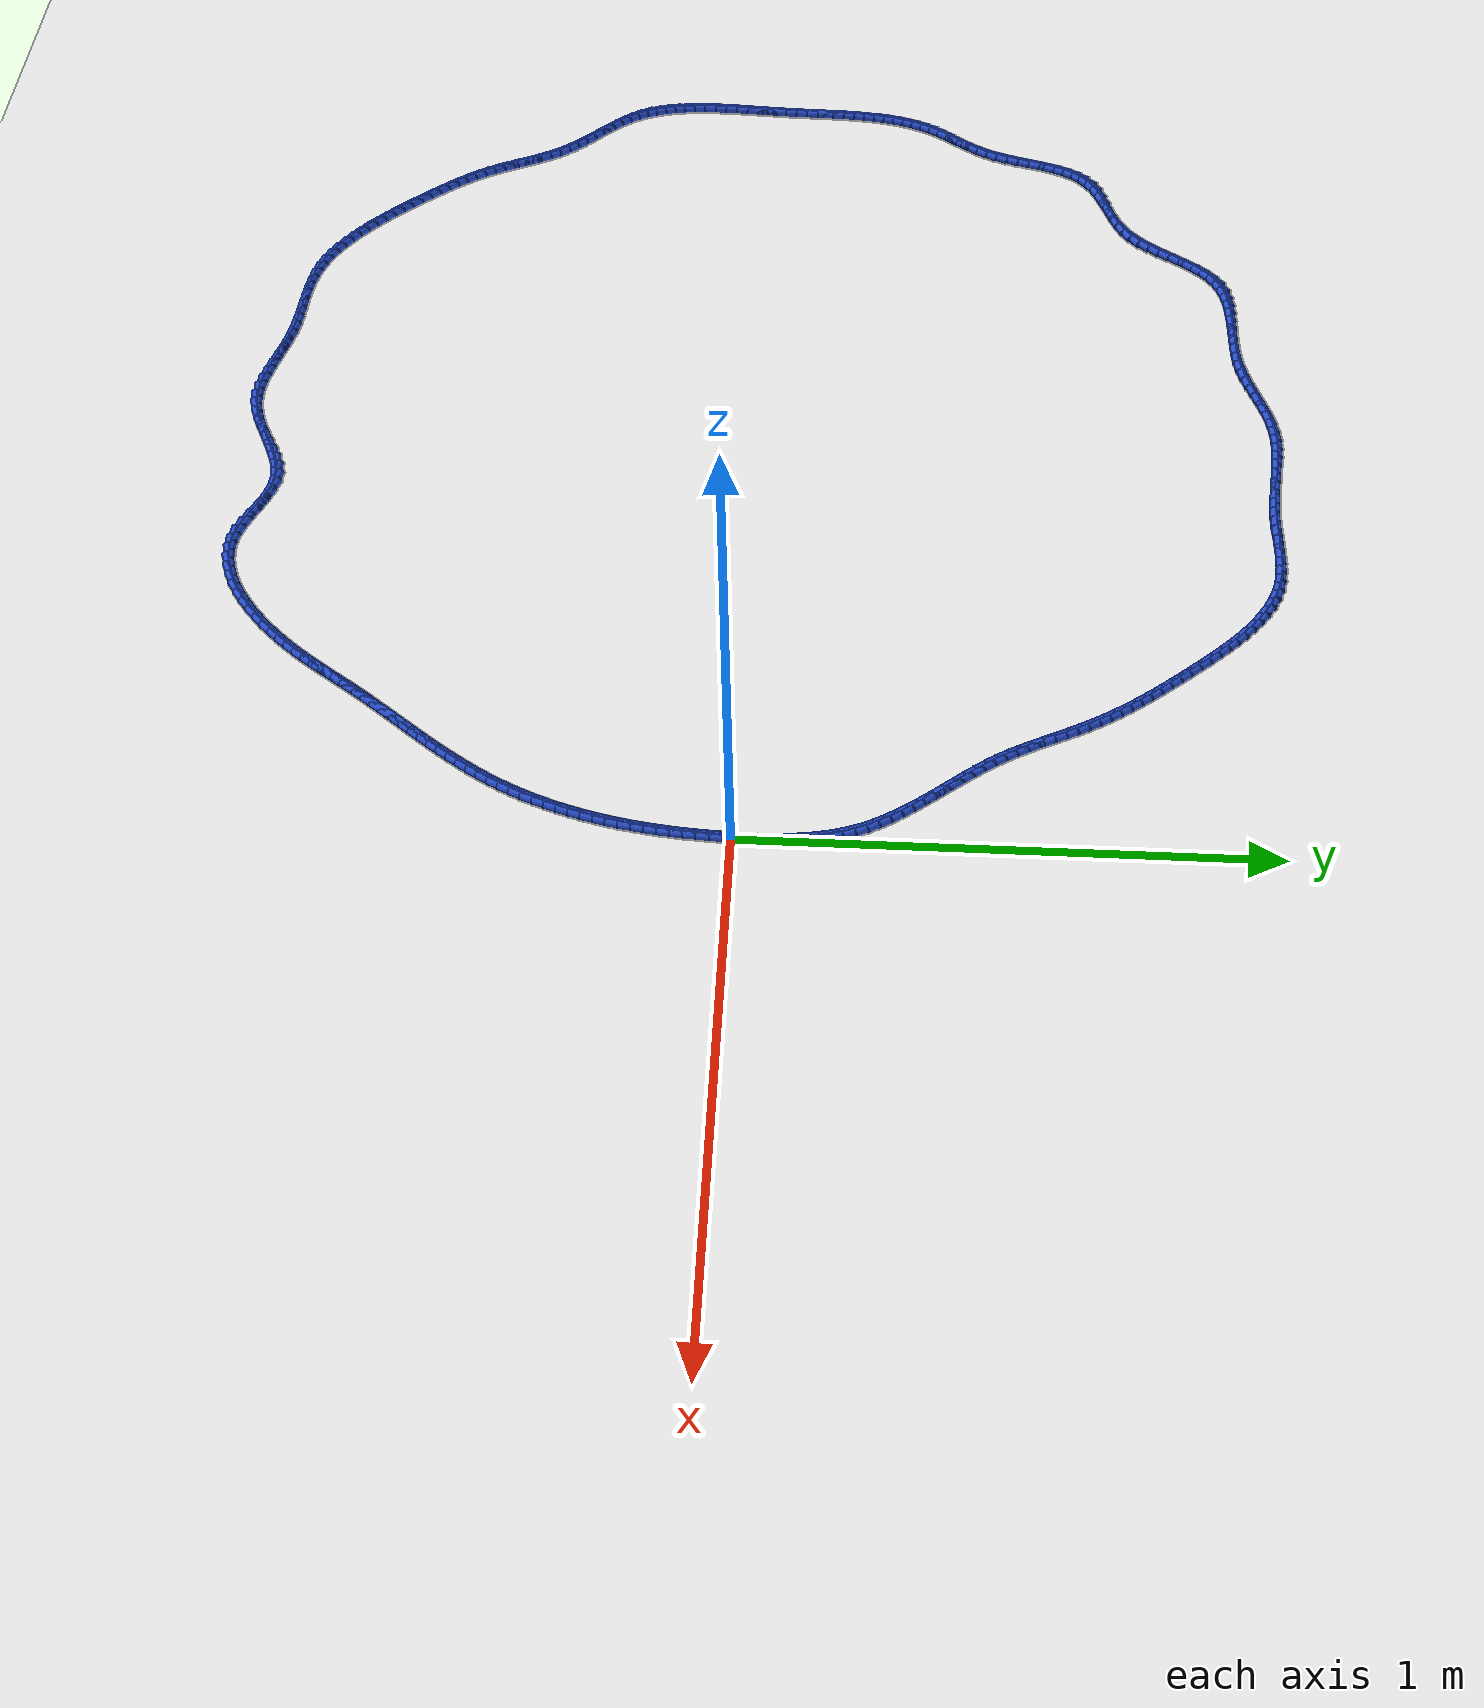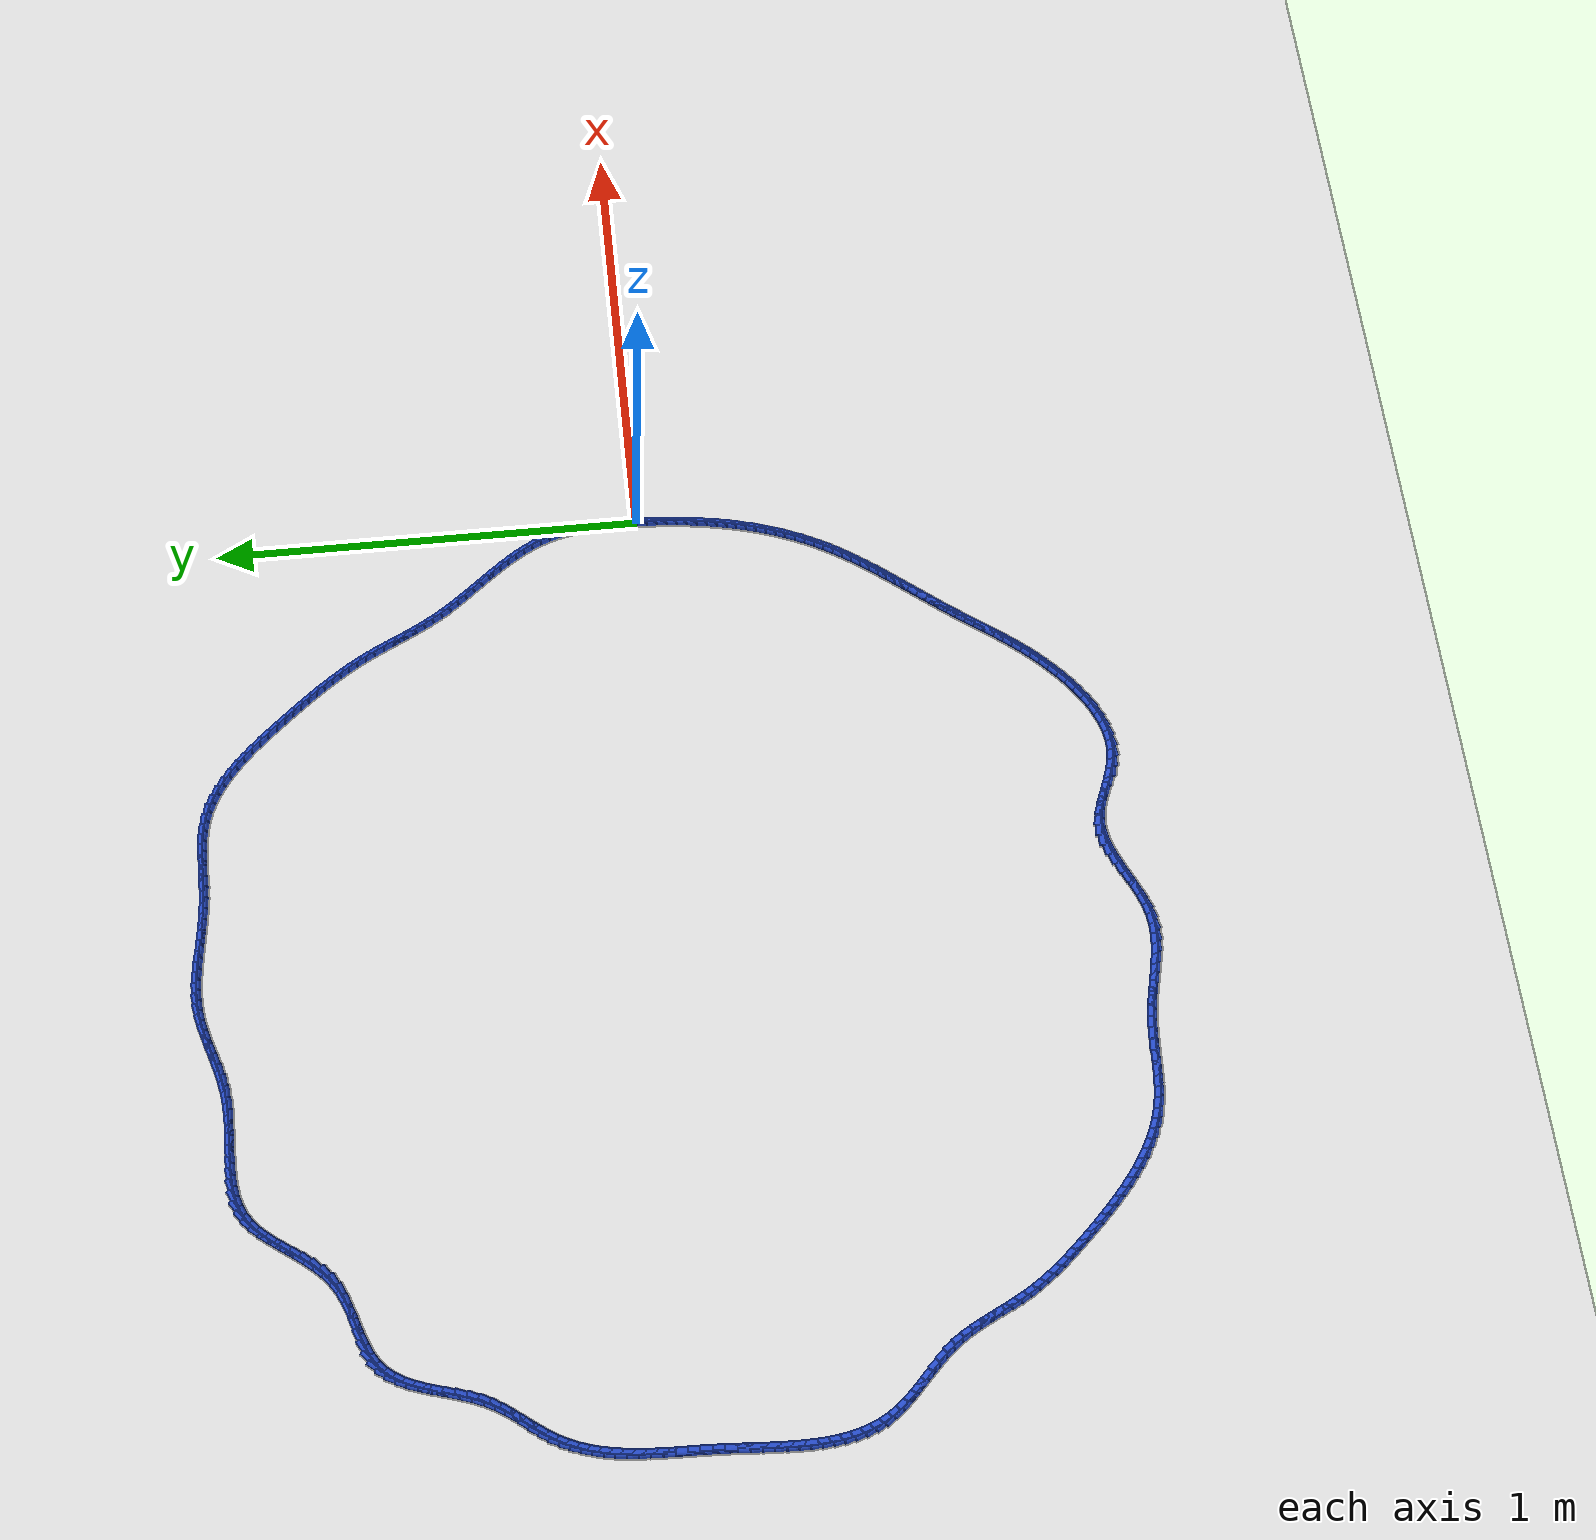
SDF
<sdf version="1.6">
 <world name="default">
  <light name="sun" type="directional">
   <pose>0 0 10 0 -0 0</pose>
   <diffuse>0.8 0.8 0.8 1</diffuse>
   <specular>0.2 0.2 0.2 1</specular>
   <attenuation>
    <range>1000</range>
    <constant>0.9</constant>
    <linear>0.01</linear>
    <quadratic>0.001</quadratic>
   </attenuation>
   <direction>-0.5 0.1 -0.9</direction>
  </light>
  <model name="ground_plane">
   <static>1</static>
   <link name="link">
    <collision name="collision">
     <geometry><plane><normal>0 0 1</normal><size>100 100</size></plane></geometry>
     <surface><friction><ode><mu>100</mu><mu2>50</mu2></ode></friction></surface>
    </collision>
    <visual name="visual">
     <cast_shadows>0</cast_shadows>
     <geometry><plane><normal>0 0 1</normal><size>100 100</size></plane></geometry>
     <material>
      <script><uri>file://media/materials/scripts/gazebo.material</uri><name>Gazebo/WhiteGlow</name></script>
     </material>
    </visual>
   </link>
  </model>
  <gravity>0 0 -9.8</gravity>
  <magnetic_field>6e-06 2.3e-05 -4.2e-05</magnetic_field>
  <atmosphere type="adiabatic"/>
  <physics name="default_physics" default="0" type="ode">
   <max_step_size>0.001</max_step_size>
   <real_time_factor>1</real_time_factor>
   <real_time_update_rate>1000</real_time_update_rate>
  </physics>
  <scene><ambient>0.4 0.4 0.4 1</ambient><background>0.7 0.7 0.7 1</background><shadows>1</shadows></scene>
  <spherical_coordinates>
   <surface_model>EARTH_WGS84</surface_model>
   <latitude_deg>0</latitude_deg>
   <longitude_deg>0</longitude_deg>
   <elevation>0</elevation>
   <heading_deg>0</heading_deg>
  </spherical_coordinates>
  <model name="line">
   <link name="link_0">
    <pose>1.5720931501039814e-18 5.551115123125783e-17 0.01 0 1.57 1.5464983713554736</pose>
    <collision name="collision">
     <geometry><cylinder><radius>0.01</radius><length>0.08</length></cylinder></geometry>
    </collision>
    <visual name="visual">
     <material>
      <script><name>Gazebo/Blue</name><uri>file://media/materials/scripts/gazebo.material</uri></script>
     </material>
     <geometry><cylinder><radius>0.01</radius><length>0.08</length></cylinder></geometry>
    </visual>
   </link>
   <link name="link_1">
    <pose>0.0005887357007303064 0.024225076726662898 0.01 0 1.57 1.5649134735716728</pose>
    <collision name="collision">
     <geometry><cylinder><radius>0.01</radius><length>0.08</length></cylinder></geometry>
    </collision>
    <visual name="visual">
     <material>
      <script><name>Gazebo/Blue</name><uri>file://media/materials/scripts/gazebo.material</uri></script>
     </material>
     <geometry><cylinder><radius>0.01</radius><length>0.08</length></cylinder></geometry>
    </visual>
   </link>
   <link name="link_2">
    <pose>0.0007316197944350821 0.048513026802965015 0.01 0 1.57 -1.5528984332686093</pose>
    <collision name="collision">
     <geometry><cylinder><radius>0.01</radius><length>0.08</length></cylinder></geometry>
    </collision>
    <visual name="visual">
     <material>
      <script><name>Gazebo/Blue</name><uri>file://media/materials/scripts/gazebo.material</uri></script>
     </material>
     <geometry><cylinder><radius>0.01</radius><length>0.08</length></cylinder></geometry>
    </visual>
   </link>
   <link name="link_3">
    <pose>0.00029726016754234353 0.07277919226686647 0.01 0 1.57 -1.523521618941803</pose>
    <collision name="collision">
     <geometry><cylinder><radius>0.01</radius><length>0.08</length></cylinder></geometry>
    </collision>
    <visual name="visual">
     <material>
      <script><name>Gazebo/Blue</name><uri>file://media/materials/scripts/gazebo.material</uri></script>
     </material>
     <geometry><cylinder><radius>0.01</radius><length>0.08</length></cylinder></geometry>
    </visual>
   </link>
   <link name="link_4">
    <pose>-0.0008457352935198898 0.0969389151563273 0.01 0 1.57 -1.4882501831795578</pose>
    <collision name="collision">
     <geometry><cylinder><radius>0.01</radius><length>0.08</length></cylinder></geometry>
    </collision>
    <visual name="visual">
     <material>
      <script><name>Gazebo/Blue</name><uri>file://media/materials/scripts/gazebo.material</uri></script>
     </material>
     <geometry><cylinder><radius>0.01</radius><length>0.08</length></cylinder></geometry>
    </visual>
   </link>
   <link name="link_5">
    <pose>-0.0028287587023236044 0.12090753750930766 0.01 0 1.57 -1.4467390822719493</pose>
    <collision name="collision">
     <geometry><cylinder><radius>0.01</radius><length>0.08</length></cylinder></geometry>
    </collision>
    <visual name="visual">
     <material>
      <script><name>Gazebo/Blue</name><uri>file://media/materials/scripts/gazebo.material</uri></script>
     </material>
     <geometry><cylinder><radius>0.01</radius><length>0.08</length></cylinder></geometry>
    </visual>
   </link>
   <link name="link_6">
    <pose>-0.0057832021724407824 0.1446004013637676 0.01 0 1.57 -1.3986288624564207</pose>
    <collision name="collision">
     <geometry><cylinder><radius>0.01</radius><length>0.08</length></cylinder></geometry>
    </collision>
    <visual name="visual">
     <material>
      <script><name>Gazebo/Blue</name><uri>file://media/materials/scripts/gazebo.material</uri></script>
     </material>
     <geometry><cylinder><radius>0.01</radius><length>0.08</length></cylinder></geometry>
    </visual>
   </link>
   <link name="link_7">
    <pose>-0.009840457817443403 0.16793284875766706 0.01 0 1.57 -1.3435927050525724</pose>
    <collision name="collision">
     <geometry><cylinder><radius>0.01</radius><length>0.08</length></cylinder></geometry>
    </collision>
    <visual name="visual">
     <material>
      <script><name>Gazebo/Blue</name><uri>file://media/materials/scripts/gazebo.material</uri></script>
     </material>
     <geometry><cylinder><radius>0.01</radius><length>0.08</length></cylinder></geometry>
    </visual>
   </link>
   <link name="link_8">
    <pose>-0.01513191775090346 0.19082022172896626 0.01 0 1.57 -1.2814021999206768</pose>
    <collision name="collision">
     <geometry><cylinder><radius>0.01</radius><length>0.08</length></cylinder></geometry>
    </collision>
    <visual name="visual">
     <material>
      <script><name>Gazebo/Blue</name><uri>file://media/materials/scripts/gazebo.material</uri></script>
     </material>
     <geometry><cylinder><radius>0.01</radius><length>0.08</length></cylinder></geometry>
    </visual>
   </link>
   <link name="link_9">
    <pose>-0.021788974086392927 0.21317786231562516 0.01 0 1.57 -1.212492922995718</pose>
    <collision name="collision">
     <geometry><cylinder><radius>0.01</radius><length>0.08</length></cylinder></geometry>
    </collision>
    <visual name="visual">
     <material>
      <script><name>Gazebo/Blue</name><uri>file://media/materials/scripts/gazebo.material</uri></script>
     </material>
     <geometry><cylinder><radius>0.01</radius><length>0.08</length></cylinder></geometry>
    </visual>
   </link>
   <link name="link_10">
    <pose>-0.029933086285535437 0.23492639995266337 0.01 0 1.57 -1.145155404982983</pose>
    <collision name="collision">
     <geometry><cylinder><radius>0.01</radius><length>0.08</length></cylinder></geometry>
    </collision>
    <visual name="visual">
     <material>
      <script><name>Gazebo/Blue</name><uri>file://media/materials/scripts/gazebo.material</uri></script>
     </material>
     <geometry><cylinder><radius>0.01</radius><length>0.08</length></cylinder></geometry>
    </visual>
   </link>
   <link name="link_11">
    <pose>-0.039520625112863805 0.2560743448843829 0.01 0 1.57 -1.0865360976006897</pose>
    <collision name="collision">
     <geometry><cylinder><radius>0.01</radius><length>0.08</length></cylinder></geometry>
    </collision>
    <visual name="visual">
     <material>
      <script><name>Gazebo/Blue</name><uri>file://media/materials/scripts/gazebo.material</uri></script>
     </material>
     <geometry><cylinder><radius>0.01</radius><length>0.08</length></cylinder></geometry>
    </visual>
   </link>
   <link name="link_12">
    <pose>-0.050371889398334986 0.27670264182178117 0.01 0 1.57 -1.0370978475238046</pose>
    <collision name="collision">
     <geometry><cylinder><radius>0.01</radius><length>0.08</length></cylinder></geometry>
    </collision>
    <visual name="visual">
     <material>
      <script><name>Gazebo/Blue</name><uri>file://media/materials/scripts/gazebo.material</uri></script>
     </material>
     <geometry><cylinder><radius>0.01</radius><length>0.08</length></cylinder></geometry>
    </visual>
   </link>
   <link name="link_13">
    <pose>-0.062303116731490735 0.29689439737488704 0.01 0 1.57 -0.9968160540351102</pose>
    <collision name="collision">
     <geometry><cylinder><radius>0.01</radius><length>0.08</length></cylinder></geometry>
    </collision>
    <visual name="visual">
     <material>
      <script><name>Gazebo/Blue</name><uri>file://media/materials/scripts/gazebo.material</uri></script>
     </material>
     <geometry><cylinder><radius>0.01</radius><length>0.08</length></cylinder></geometry>
    </visual>
   </link>
   <link name="link_14">
    <pose>-0.07513054470187269 0.31673271815372955 0.01 0 1.57 -0.9655006327158399</pose>
    <collision name="collision">
     <geometry><cylinder><radius>0.01</radius><length>0.08</length></cylinder></geometry>
    </collision>
    <visual name="visual">
     <material>
      <script><name>Gazebo/Blue</name><uri>file://media/materials/scripts/gazebo.material</uri></script>
     </material>
     <geometry><cylinder><radius>0.01</radius><length>0.08</length></cylinder></geometry>
    </visual>
   </link>
   <link name="link_15">
    <pose>-0.08867041089902265 0.33630071076833773 0.01 0 1.57 -0.9428971027956308</pose>
    <collision name="collision">
     <geometry><cylinder><radius>0.01</radius><length>0.08</length></cylinder></geometry>
    </collision>
    <visual name="visual">
     <material>
      <script><name>Gazebo/Blue</name><uri>file://media/materials/scripts/gazebo.material</uri></script>
     </material>
     <geometry><cylinder><radius>0.01</radius><length>0.08</length></cylinder></geometry>
    </visual>
   </link>
   <link name="link_16">
    <pose>-0.1027389529124823 0.3556814818287406 0.01 0 1.57 -0.9287588735910989</pose>
    <collision name="collision">
     <geometry><cylinder><radius>0.01</radius><length>0.08</length></cylinder></geometry>
    </collision>
    <visual name="visual">
     <material>
      <script><name>Gazebo/Blue</name><uri>file://media/materials/scripts/gazebo.material</uri></script>
     </material>
     <geometry><cylinder><radius>0.01</radius><length>0.08</length></cylinder></geometry>
    </visual>
   </link>
   <link name="link_17">
    <pose>-0.11715240833179337 0.374958137944967 0.01 0 1.57 -0.9228936057417596</pose>
    <collision name="collision">
     <geometry><cylinder><radius>0.01</radius><length>0.08</length></cylinder></geometry>
    </collision>
    <visual name="visual">
     <material>
      <script><name>Gazebo/Blue</name><uri>file://media/materials/scripts/gazebo.material</uri></script>
     </material>
     <geometry><cylinder><radius>0.01</radius><length>0.08</length></cylinder></geometry>
    </visual>
   </link>
   <link name="link_18">
    <pose>-0.13172701474649756 0.39421378572704613 0.01 0 1.57 -0.9251886453365027</pose>
    <collision name="collision">
     <geometry><cylinder><radius>0.01</radius><length>0.08</length></cylinder></geometry>
    </collision>
    <visual name="visual">
     <material>
      <script><name>Gazebo/Blue</name><uri>file://media/materials/scripts/gazebo.material</uri></script>
     </material>
     <geometry><cylinder><radius>0.01</radius><length>0.08</length></cylinder></geometry>
    </visual>
   </link>
   <link name="link_19">
    <pose>-0.1462790097461366 0.41353153178500673 0.01 0 1.57 -0.935619777375196</pose>
    <collision name="collision">
     <geometry><cylinder><radius>0.01</radius><length>0.08</length></cylinder></geometry>
    </collision>
    <visual name="visual">
     <material>
      <script><name>Gazebo/Blue</name><uri>file://media/materials/scripts/gazebo.material</uri></script>
     </material>
     <geometry><cylinder><radius>0.01</radius><length>0.08</length></cylinder></geometry>
    </visual>
   </link>
   <link name="link_20">
    <pose>-0.16062463092025225 0.4329944827288781 0.01 0 1.57 -0.9542455594178907</pose>
    <collision name="collision">
     <geometry><cylinder><radius>0.01</radius><length>0.08</length></cylinder></geometry>
    </collision>
    <visual name="visual">
     <material>
      <script><name>Gazebo/Blue</name><uri>file://media/materials/scripts/gazebo.material</uri></script>
     </material>
     <geometry><cylinder><radius>0.01</radius><length>0.08</length></cylinder></geometry>
    </visual>
   </link>
   <link name="link_21">
    <pose>-0.17458011585838615 0.45268574516868887 0.01 0 1.57 -0.9811872266130017</pose>
    <collision name="collision">
     <geometry><cylinder><radius>0.01</radius><length>0.08</length></cylinder></geometry>
    </collision>
    <visual name="visual">
     <material>
      <script><name>Gazebo/Blue</name><uri>file://media/materials/scripts/gazebo.material</uri></script>
     </material>
     <geometry><cylinder><radius>0.01</radius><length>0.08</length></cylinder></geometry>
    </visual>
   </link>
   <link name="link_22">
    <pose>-0.18796170215008004 0.4726884257144683 0.01 0 1.57 -1.0165704666686322</pose>
    <collision name="collision">
     <geometry><cylinder><radius>0.01</radius><length>0.08</length></cylinder></geometry>
    </collision>
    <visual name="visual">
     <material>
      <script><name>Gazebo/Blue</name><uri>file://media/materials/scripts/gazebo.material</uri></script>
     </material>
     <geometry><cylinder><radius>0.01</radius><length>0.08</length></cylinder></geometry>
    </visual>
   </link>
   <link name="link_23">
    <pose>-0.20058609032451905 0.4930853885777595 0.01 0 1.57 -1.0556218456720694</pose>
    <collision name="collision">
     <geometry><cylinder><radius>0.01</radius><length>0.08</length></cylinder></geometry>
    </collision>
    <visual name="visual">
     <material>
      <script><name>Gazebo/Blue</name><uri>file://media/materials/scripts/gazebo.material</uri></script>
     </material>
     <geometry><cylinder><radius>0.01</radius><length>0.08</length></cylinder></geometry>
    </visual>
   </link>
   <link name="link_24">
    <pose>-0.21237368340686863 0.5139051986065156 0.01 0 1.57 -1.0872623813494495</pose>
    <collision name="collision">
     <geometry><cylinder><radius>0.01</radius><length>0.08</length></cylinder></geometry>
    </collision>
    <visual name="visual">
     <material>
      <script><name>Gazebo/Blue</name><uri>file://media/materials/scripts/gazebo.material</uri></script>
     </material>
     <geometry><cylinder><radius>0.01</radius><length>0.08</length></cylinder></geometry>
    </visual>
   </link>
   <link name="link_25">
    <pose>-0.22347904998644763 0.5350538098958054 0.01 0 1.57 -1.1099023591005426</pose>
    <collision name="collision">
     <geometry><cylinder><radius>0.01</radius><length>0.08</length></cylinder></geometry>
    </collision>
    <visual name="visual">
     <material>
      <script><name>Gazebo/Blue</name><uri>file://media/materials/scripts/gazebo.material</uri></script>
     </material>
     <geometry><cylinder><radius>0.01</radius><length>0.08</length></cylinder></geometry>
    </visual>
   </link>
   <link name="link_26">
    <pose>-0.2340888799992537 0.5564203575753895 0.01 0 1.57 -1.1235168623400216</pose>
    <collision name="collision">
     <geometry><cylinder><radius>0.01</radius><length>0.08</length></cylinder></geometry>
    </collision>
    <visual name="visual">
     <material>
      <script><name>Gazebo/Blue</name><uri>file://media/materials/scripts/gazebo.material</uri></script>
     </material>
     <geometry><cylinder><radius>0.01</radius><length>0.08</length></cylinder></geometry>
    </visual>
   </link>
   <link name="link_27">
    <pose>-0.2443898633812844 0.5778939767750282 0.01 0 1.57 -1.1280832406296324</pose>
    <collision name="collision">
     <geometry><cylinder><radius>0.01</radius><length>0.08</length></cylinder></geometry>
    </collision>
    <visual name="visual">
     <material>
      <script><name>Gazebo/Blue</name><uri>file://media/materials/scripts/gazebo.material</uri></script>
     </material>
     <geometry><cylinder><radius>0.01</radius><length>0.08</length></cylinder></geometry>
    </visual>
   </link>
   <link name="link_28">
    <pose>-0.25456869006853733 0.5993638026244821 0.01 0 1.57 -1.1235473831009095</pose>
    <collision name="collision">
     <geometry><cylinder><radius>0.01</radius><length>0.08</length></cylinder></geometry>
    </collision>
    <visual name="visual">
     <material>
      <script><name>Gazebo/Blue</name><uri>file://media/materials/scripts/gazebo.material</uri></script>
     </material>
     <geometry><cylinder><radius>0.01</radius><length>0.08</length></cylinder></geometry>
    </visual>
   </link>
   <link name="link_29">
    <pose>-0.26481204999701013 0.6207189702535117 0.01 0 1.57 -1.1098116122723358</pose>
    <collision name="collision">
     <geometry><cylinder><radius>0.01</radius><length>0.08</length></cylinder></geometry>
    </collision>
    <visual name="visual">
     <material>
      <script><name>Gazebo/Blue</name><uri>file://media/materials/scripts/gazebo.material</uri></script>
     </material>
     <geometry><cylinder><radius>0.01</radius><length>0.08</length></cylinder></geometry>
    </visual>
   </link>
   <link name="link_30">
    <pose>-0.2753066331027002 0.6418486147918769 0.01 0 1.57 -1.086758794405584</pose>
    <collision name="collision">
     <geometry><cylinder><radius>0.01</radius><length>0.08</length></cylinder></geometry>
    </collision>
    <visual name="visual">
     <material>
      <script><name>Gazebo/Blue</name><uri>file://media/materials/scripts/gazebo.material</uri></script>
     </material>
     <geometry><cylinder><radius>0.01</radius><length>0.08</length></cylinder></geometry>
    </visual>
   </link>
   <link name="link_31">
    <pose>-0.28623886736249976 0.6626420734082432 0.01 0 1.57 -1.0574428520418497</pose>
    <collision name="collision">
     <geometry><cylinder><radius>0.01</radius><length>0.08</length></cylinder></geometry>
    </collision>
    <visual name="visual">
     <material>
      <script><name>Gazebo/Blue</name><uri>file://media/materials/scripts/gazebo.material</uri></script>
     </material>
     <geometry><cylinder><radius>0.01</radius><length>0.08</length></cylinder></geometry>
    </visual>
   </link>
   <link name="link_32">
    <pose>-0.297735583628606 0.68303464822363 0.01 0 1.57 -1.0291176153465829</pose>
    <collision name="collision">
     <geometry><cylinder><radius>0.01</radius><length>0.08</length></cylinder></geometry>
    </collision>
    <visual name="visual">
     <material>
      <script><name>Gazebo/Blue</name><uri>file://media/materials/scripts/gazebo.material</uri></script>
     </material>
     <geometry><cylinder><radius>0.01</radius><length>0.08</length></cylinder></geometry>
    </visual>
   </link>
   <link name="link_33">
    <pose>-0.3097885913738731 0.7030657781156517 0.01 0 1.57 -1.002941183865782</pose>
    <collision name="collision">
     <geometry><cylinder><radius>0.01</radius><length>0.08</length></cylinder></geometry>
    </collision>
    <visual name="visual">
     <material>
      <script><name>Gazebo/Blue</name><uri>file://media/materials/scripts/gazebo.material</uri></script>
     </material>
     <geometry><cylinder><radius>0.01</radius><length>0.08</length></cylinder></geometry>
    </visual>
   </link>
   <link name="link_34">
    <pose>-0.32237110842961614 0.7227892409744509 0.01 0 1.57 -0.9790506794853427</pose>
    <collision name="collision">
     <geometry><cylinder><radius>0.01</radius><length>0.08</length></cylinder></geometry>
    </collision>
    <visual name="visual">
     <material>
      <script><name>Gazebo/Blue</name><uri>file://media/materials/scripts/gazebo.material</uri></script>
     </material>
     <geometry><cylinder><radius>0.01</radius><length>0.08</length></cylinder></geometry>
    </visual>
   </link>
   <link name="link_35">
    <pose>-0.3354563526271495 0.7422588146901686 0.01 0 1.57 -0.957547431150505</pose>
    <collision name="collision">
     <geometry><cylinder><radius>0.01</radius><length>0.08</length></cylinder></geometry>
    </collision>
    <visual name="visual">
     <material>
      <script><name>Gazebo/Blue</name><uri>file://media/materials/scripts/gazebo.material</uri></script>
     </material>
     <geometry><cylinder><radius>0.01</radius><length>0.08</length></cylinder></geometry>
    </visual>
   </link>
   <link name="link_36">
    <pose>-0.34901754179778793 0.7615282771529474 0.01 0 1.57 -0.9384990975968414</pose>
    <collision name="collision">
     <geometry><cylinder><radius>0.01</radius><length>0.08</length></cylinder></geometry>
    </collision>
    <visual name="visual">
     <material>
      <script><name>Gazebo/Blue</name><uri>file://media/materials/scripts/gazebo.material</uri></script>
     </material>
     <geometry><cylinder><radius>0.01</radius><length>0.08</length></cylinder></geometry>
    </visual>
   </link>
   <link name="link_37">
    <pose>-0.3630278937728464 0.7806514062529294 0.01 0 1.57 -0.9219426738590444</pose>
    <collision name="collision">
     <geometry><cylinder><radius>0.01</radius><length>0.08</length></cylinder></geometry>
    </collision>
    <visual name="visual">
     <material>
      <script><name>Gazebo/Blue</name><uri>file://media/materials/scripts/gazebo.material</uri></script>
     </material>
     <geometry><cylinder><radius>0.01</radius><length>0.08</length></cylinder></geometry>
    </visual>
   </link>
   <link name="link_38">
    <pose>-0.3774606263836391 0.7996819798802559 0.01 0 1.57 -0.9078879918364929</pose>
    <collision name="collision">
     <geometry><cylinder><radius>0.01</radius><length>0.08</length></cylinder></geometry>
    </collision>
    <visual name="visual">
     <material>
      <script><name>Gazebo/Blue</name><uri>file://media/materials/scripts/gazebo.material</uri></script>
     </material>
     <geometry><cylinder><radius>0.01</radius><length>0.08</length></cylinder></geometry>
    </visual>
   </link>
   <link name="link_39">
    <pose>-0.392288957461481 0.8186737759250691 0.01 0 1.57 -0.8963213827988467</pose>
    <collision name="collision">
     <geometry><cylinder><radius>0.01</radius><length>0.08</length></cylinder></geometry>
    </collision>
    <visual name="visual">
     <material>
      <script><name>Gazebo/Blue</name><uri>file://media/materials/scripts/gazebo.material</uri></script>
     </material>
     <geometry><cylinder><radius>0.01</radius><length>0.08</length></cylinder></geometry>
    </visual>
   </link>
   <link name="link_40">
    <pose>-0.40748610483768677 0.8376805722775111 0.01 0 1.57 -0.8872092454545766</pose>
    <collision name="collision">
     <geometry><cylinder><radius>0.01</radius><length>0.08</length></cylinder></geometry>
    </collision>
    <visual name="visual">
     <material>
      <script><name>Gazebo/Blue</name><uri>file://media/materials/scripts/gazebo.material</uri></script>
     </material>
     <geometry><cylinder><radius>0.01</radius><length>0.08</length></cylinder></geometry>
    </visual>
   </link>
   <link name="link_41">
    <pose>-0.42302528634357095 0.8567561468277236 0.01 0 1.57 -0.8797433199122261</pose>
    <collision name="collision">
     <geometry><cylinder><radius>0.01</radius><length>0.08</length></cylinder></geometry>
    </collision>
    <visual name="visual">
     <material>
      <script><name>Gazebo/Blue</name><uri>file://media/materials/scripts/gazebo.material</uri></script>
     </material>
     <geometry><cylinder><radius>0.01</radius><length>0.08</length></cylinder></geometry>
    </visual>
   </link>
   <link name="link_42">
    <pose>-0.4388851222924729 0.8759311966488835 0.01 0 1.57 -0.8683331694966139</pose>
    <collision name="collision">
     <geometry><cylinder><radius>0.01</radius><length>0.08</length></cylinder></geometry>
    </collision>
    <visual name="visual">
     <material>
      <script><name>Gazebo/Blue</name><uri>file://media/materials/scripts/gazebo.material</uri></script>
     </material>
     <geometry><cylinder><radius>0.01</radius><length>0.08</length></cylinder></geometry>
    </visual>
   </link>
   <link name="link_43">
    <pose>-0.45508385393727074 0.8950671477922065 0.01 0 1.57 -0.8504401230253983</pose>
    <collision name="collision">
     <geometry><cylinder><radius>0.01</radius><length>0.08</length></cylinder></geometry>
    </collision>
    <visual name="visual">
     <material>
      <script><name>Gazebo/Blue</name><uri>file://media/materials/scripts/gazebo.material</uri></script>
     </material>
     <geometry><cylinder><radius>0.01</radius><length>0.08</length></cylinder></geometry>
    </visual>
   </link>
   <link name="link_44">
    <pose>-0.47165736141588394 0.9139500683761572 0.01 0 1.57 -0.8258104740875727</pose>
    <collision name="collision">
     <geometry><cylinder><radius>0.01</radius><length>0.08</length></cylinder></geometry>
    </collision>
    <visual name="visual">
     <material>
      <script><name>Gazebo/Blue</name><uri>file://media/materials/scripts/gazebo.material</uri></script>
     </material>
     <geometry><cylinder><radius>0.01</radius><length>0.08</length></cylinder></geometry>
    </visual>
   </link>
   <link name="link_45">
    <pose>-0.4886416055428532 0.9323656818475615 0.01 0 1.57 -0.7940169877237658</pose>
    <collision name="collision">
     <geometry><cylinder><radius>0.01</radius><length>0.08</length></cylinder></geometry>
    </collision>
    <visual name="visual">
     <material>
      <script><name>Gazebo/Blue</name><uri>file://media/materials/scripts/gazebo.material</uri></script>
     </material>
     <geometry><cylinder><radius>0.01</radius><length>0.08</length></cylinder></geometry>
    </visual>
   </link>
   <link name="link_46">
    <pose>-0.5060725471327198 0.9500997116532452 0.01 0 1.57 -0.754461978098026</pose>
    <collision name="collision">
     <geometry><cylinder><radius>0.01</radius><length>0.08</length></cylinder></geometry>
    </collision>
    <visual name="visual">
     <material>
      <script><name>Gazebo/Blue</name><uri>file://media/materials/scripts/gazebo.material</uri></script>
     </material>
     <geometry><cylinder><radius>0.01</radius><length>0.08</length></cylinder></geometry>
    </visual>
   </link>
   <link name="link_47">
    <pose>-0.5239861470000243 0.9669378812400347 0.01 0 1.57 -0.7064011280596505</pose>
    <collision name="collision">
     <geometry><cylinder><radius>0.01</radius><length>0.08</length></cylinder></geometry>
    </collision>
    <visual name="visual">
     <material>
      <script><name>Gazebo/Blue</name><uri>file://media/materials/scripts/gazebo.material</uri></script>
     </material>
     <geometry><cylinder><radius>0.01</radius><length>0.08</length></cylinder></geometry>
    </visual>
   </link>
   <link name="link_48">
    <pose>-0.5424183659593079 0.9826659140547551 0.01 0 1.57 -0.6489902450254843</pose>
    <collision name="collision">
     <geometry><cylinder><radius>0.01</radius><length>0.08</length></cylinder></geometry>
    </collision>
    <visual name="visual">
     <material>
      <script><name>Gazebo/Blue</name><uri>file://media/materials/scripts/gazebo.material</uri></script>
     </material>
     <geometry><cylinder><radius>0.01</radius><length>0.08</length></cylinder></geometry>
    </visual>
   </link>
   <link name="link_49">
    <pose>-0.5614051648251114 0.9970695335442326 0.01 0 1.57 -0.5813737888308368</pose>
    <collision name="collision">
     <geometry><cylinder><radius>0.01</radius><length>0.08</length></cylinder></geometry>
    </collision>
    <visual name="visual">
     <material>
      <script><name>Gazebo/Blue</name><uri>file://media/materials/scripts/gazebo.material</uri></script>
     </material>
     <geometry><cylinder><radius>0.01</radius><length>0.08</length></cylinder></geometry>
    </visual>
   </link>
   <link name="link_50">
    <pose>-0.580982504411976 1.0099344631552933 0.01 0 1.57 -0.5028375322086273</pose>
    <collision name="collision">
     <geometry><cylinder><radius>0.01</radius><length>0.08</length></cylinder></geometry>
    </collision>
    <visual name="visual">
     <material>
      <script><name>Gazebo/Blue</name><uri>file://media/materials/scripts/gazebo.material</uri></script>
     </material>
     <geometry><cylinder><radius>0.01</radius><length>0.08</length></cylinder></geometry>
    </visual>
   </link>
   <link name="link_51">
    <pose>-0.6011863455344423 1.0210464263347632 0.01 0 1.57 -0.41304229700559014</pose>
    <collision name="collision">
     <geometry><cylinder><radius>0.01</radius><length>0.08</length></cylinder></geometry>
    </collision>
    <visual name="visual">
     <material>
      <script><name>Gazebo/Blue</name><uri>file://media/materials/scripts/gazebo.material</uri></script>
     </material>
     <geometry><cylinder><radius>0.01</radius><length>0.08</length></cylinder></geometry>
    </visual>
   </link>
   <link name="link_52">
    <pose>-0.6220526490070517 1.030191146529468 0.01 0 1.57 -0.3123310548744103</pose>
    <collision name="collision">
     <geometry><cylinder><radius>0.01</radius><length>0.08</length></cylinder></geometry>
    </collision>
    <visual name="visual">
     <material>
      <script><name>Gazebo/Blue</name><uri>file://media/materials/scripts/gazebo.material</uri></script>
     </material>
     <geometry><cylinder><radius>0.01</radius><length>0.08</length></cylinder></geometry>
    </visual>
   </link>
   <link name="link_53">
    <pose>-0.6436173672672828 1.0371543870281485 0.01 0 1.57 -0.20803774556017843</pose>
    <collision name="collision">
     <geometry><cylinder><radius>0.01</radius><length>0.08</length></cylinder></geometry>
    </collision>
    <visual name="visual">
     <material>
      <script><name>Gazebo/Blue</name><uri>file://media/materials/scripts/gazebo.material</uri></script>
     </material>
     <geometry><cylinder><radius>0.01</radius><length>0.08</length></cylinder></geometry>
    </visual>
   </link>
   <link name="link_54">
    <pose>-0.6658883416980451 1.0418556093421882 0.01 0 1.57 -0.1212937171855763</pose>
    <collision name="collision">
     <geometry><cylinder><radius>0.01</radius><length>0.08</length></cylinder></geometry>
    </collision>
    <visual name="visual">
     <material>
      <script><name>Gazebo/Blue</name><uri>file://media/materials/scripts/gazebo.material</uri></script>
     </material>
     <geometry><cylinder><radius>0.01</radius><length>0.08</length></cylinder></geometry>
    </visual>
   </link>
   <link name="link_55">
    <pose>-0.6887825904872125 1.044646236712495 0.01 0 1.57 -0.05624902360117668</pose>
    <collision name="collision">
     <geometry><cylinder><radius>0.01</radius><length>0.08</length></cylinder></geometry>
    </collision>
    <visual name="visual">
     <material>
      <script><name>Gazebo/Blue</name><uri>file://media/materials/scripts/gazebo.material</uri></script>
     </material>
     <geometry><cylinder><radius>0.01</radius><length>0.08</length></cylinder></geometry>
    </visual>
   </link>
   <link name="link_56">
    <pose>-0.7121988235532964 1.045964767842309 0.01 0 1.57 -0.011952883846207981</pose>
    <collision name="collision">
     <geometry><cylinder><radius>0.01</radius><length>0.08</length></cylinder></geometry>
    </collision>
    <visual name="visual">
     <material>
      <script><name>Gazebo/Blue</name><uri>file://media/materials/scripts/gazebo.material</uri></script>
     </material>
     <geometry><cylinder><radius>0.01</radius><length>0.08</length></cylinder></geometry>
    </visual>
   </link>
   <link name="link_57">
    <pose>-0.7360357508148085 1.046249701434869 0.01 0 1.57 0.012839209454055252</pose>
    <collision name="collision">
     <geometry><cylinder><radius>0.01</radius><length>0.08</length></cylinder></geometry>
    </collision>
    <visual name="visual">
     <material>
      <script><name>Gazebo/Blue</name><uri>file://media/materials/scripts/gazebo.material</uri></script>
     </material>
     <geometry><cylinder><radius>0.01</radius><length>0.08</length></cylinder></geometry>
    </visual>
   </link>
   <link name="link_58">
    <pose>-0.7601920821902609 1.0459395361934167 0.01 0 1.57 0.01914744399157125</pose>
    <collision name="collision">
     <geometry><cylinder><radius>0.01</radius><length>0.08</length></cylinder></geometry>
    </collision>
    <visual name="visual">
     <material>
      <script><name>Gazebo/Blue</name><uri>file://media/materials/scripts/gazebo.material</uri></script>
     </material>
     <geometry><cylinder><radius>0.01</radius><length>0.08</length></cylinder></geometry>
    </visual>
   </link>
   <link name="link_59">
    <pose>-0.7845665275981649 1.0454727708211913 0.01 0 1.57 0.007548130158248473</pose>
    <collision name="collision">
     <geometry><cylinder><radius>0.01</radius><length>0.08</length></cylinder></geometry>
    </collision>
    <visual name="visual">
     <material>
      <script><name>Gazebo/Blue</name><uri>file://media/materials/scripts/gazebo.material</uri></script>
     </material>
     <geometry><cylinder><radius>0.01</radius><length>0.08</length></cylinder></geometry>
    </visual>
   </link>
   <link name="link_60">
    <pose>-0.8090577969570325 1.045287904021433 0.01 0 1.57 -0.021848841422465175</pose>
    <collision name="collision">
     <geometry><cylinder><radius>0.01</radius><length>0.08</length></cylinder></geometry>
    </collision>
    <visual name="visual">
     <material>
      <script><name>Gazebo/Blue</name><uri>file://media/materials/scripts/gazebo.material</uri></script>
     </material>
     <geometry><cylinder><radius>0.01</radius><length>0.08</length></cylinder></geometry>
    </visual>
   </link>
   <link name="link_61">
    <pose>-0.8335646001853753 1.0458234344973811 0.01 0 1.57 -0.06450331492207673</pose>
    <collision name="collision">
     <geometry><cylinder><radius>0.01</radius><length>0.08</length></cylinder></geometry>
    </collision>
    <visual name="visual">
     <material>
      <script><name>Gazebo/Blue</name><uri>file://media/materials/scripts/gazebo.material</uri></script>
     </material>
     <geometry><cylinder><radius>0.01</radius><length>0.08</length></cylinder></geometry>
    </visual>
   </link>
   <link name="link_62">
    <pose>-0.8579981906236264 1.0474016715286494 0.01 0 1.57 -0.09980188473148736</pose>
    <collision name="collision">
     <geometry><cylinder><radius>0.01</radius><length>0.08</length></cylinder></geometry>
    </collision>
    <visual name="visual">
     <material>
      <script><name>Gazebo/Blue</name><uri>file://media/materials/scripts/gazebo.material</uri></script>
     </material>
     <geometry><cylinder><radius>0.01</radius><length>0.08</length></cylinder></geometry>
    </visual>
   </link>
   <link name="link_63">
    <pose>-0.8823245922556289 1.0498375852070811 0.01 0 1.57 -0.12212069396544734</pose>
    <collision name="collision">
     <geometry><cylinder><radius>0.01</radius><length>0.08</length></cylinder></geometry>
    </collision>
    <visual name="visual">
     <material>
      <script><name>Gazebo/Blue</name><uri>file://media/materials/scripts/gazebo.material</uri></script>
     </material>
     <geometry><cylinder><radius>0.01</radius><length>0.08</length></cylinder></geometry>
    </visual>
   </link>
   <link name="link_64">
    <pose>-0.9065247743418238 1.0528077078772458 0.01 0 1.57 -0.13147046762292627</pose>
    <collision name="collision">
     <geometry><cylinder><radius>0.01</radius><length>0.08</length></cylinder></geometry>
    </collision>
    <visual name="visual">
     <material>
      <script><name>Gazebo/Blue</name><uri>file://media/materials/scripts/gazebo.material</uri></script>
     </material>
     <geometry><cylinder><radius>0.01</radius><length>0.08</length></cylinder></geometry>
    </visual>
   </link>
   <link name="link_65">
    <pose>-0.9305797064842276 1.0559885687197166 0.01 0 1.57 -0.1277246841388082</pose>
    <collision name="collision">
     <geometry><cylinder><radius>0.01</radius><length>0.08</length></cylinder></geometry>
    </collision>
    <visual name="visual">
     <material>
      <script><name>Gazebo/Blue</name><uri>file://media/materials/scripts/gazebo.material</uri></script>
     </material>
     <geometry><cylinder><radius>0.01</radius><length>0.08</length></cylinder></geometry>
    </visual>
   </link>
   <link name="link_66">
    <pose>-0.9544703582848556 1.0590566969150663 0.01 0 1.57 -0.1105645420652227</pose>
    <collision name="collision">
     <geometry><cylinder><radius>0.01</radius><length>0.08</length></cylinder></geometry>
    </collision>
    <visual name="visual">
     <material>
      <script><name>Gazebo/Blue</name><uri>file://media/materials/scripts/gazebo.material</uri></script>
     </material>
     <geometry><cylinder><radius>0.01</radius><length>0.08</length></cylinder></geometry>
    </visual>
   </link>
   <link name="link_67">
    <pose>-0.9781776993457239 1.0616886216438692 0.01 0 1.57 -0.07948546546250446</pose>
    <collision name="collision">
     <geometry><cylinder><radius>0.01</radius><length>0.08</length></cylinder></geometry>
    </collision>
    <visual name="visual">
     <material>
      <script><name>Gazebo/Blue</name><uri>file://media/materials/scripts/gazebo.material</uri></script>
     </material>
     <geometry><cylinder><radius>0.01</radius><length>0.08</length></cylinder></geometry>
    </visual>
   </link>
   <link name="link_68">
    <pose>-1.001682699268848 1.063560872086698 0.01 0 1.57 -0.03387802838676995</pose>
    <collision name="collision">
     <geometry><cylinder><radius>0.01</radius><length>0.08</length></cylinder></geometry>
    </collision>
    <visual name="visual">
     <material>
      <script><name>Gazebo/Blue</name><uri>file://media/materials/scripts/gazebo.material</uri></script>
     </material>
     <geometry><cylinder><radius>0.01</radius><length>0.08</length></cylinder></geometry>
    </visual>
   </link>
   <link name="link_69">
    <pose>-1.024966327656244 1.0643499774241265 0.01 0 1.57 0.026791510075852655</pose>
    <collision name="collision">
     <geometry><cylinder><radius>0.01</radius><length>0.08</length></cylinder></geometry>
    </collision>
    <visual name="visual">
     <material>
      <script><name>Gazebo/Blue</name><uri>file://media/materials/scripts/gazebo.material</uri></script>
     </material>
     <geometry><cylinder><radius>0.01</radius><length>0.08</length></cylinder></geometry>
    </visual>
   </link>
   <link name="link_70">
    <pose>-1.0480095541099272 1.0637324668367272 0.01 0 1.57 0.10267569243208971</pose>
    <collision name="collision">
     <geometry><cylinder><radius>0.01</radius><length>0.08</length></cylinder></geometry>
    </collision>
    <visual name="visual">
     <material>
      <script><name>Gazebo/Blue</name><uri>file://media/materials/scripts/gazebo.material</uri></script>
     </material>
     <geometry><cylinder><radius>0.01</radius><length>0.08</length></cylinder></geometry>
    </visual>
   </link>
   <link name="link_71">
    <pose>-1.070793348231914 1.061384869505074 0.01 0 1.57 0.1888888307071484</pose>
    <collision name="collision">
     <geometry><cylinder><radius>0.01</radius><length>0.08</length></cylinder></geometry>
    </collision>
    <visual name="visual">
     <material>
      <script><name>Gazebo/Blue</name><uri>file://media/materials/scripts/gazebo.material</uri></script>
     </material>
     <geometry><cylinder><radius>0.01</radius><length>0.08</length></cylinder></geometry>
    </visual>
   </link>
   <link name="link_72">
    <pose>-1.0933150167962022 1.057079451329948 0.01 0 1.57 0.26054772362553597</pose>
    <collision name="collision">
     <geometry><cylinder><radius>0.01</radius><length>0.08</length></cylinder></geometry>
    </collision>
    <visual name="visual">
     <material>
      <script><name>Gazebo/Blue</name><uri>file://media/materials/scripts/gazebo.material</uri></script>
     </material>
     <geometry><cylinder><radius>0.01</radius><length>0.08</length></cylinder></geometry>
    </visual>
   </link>
   <link name="link_73">
    <pose>-1.115662799674517 1.0511213511318878 0.01 0 1.57 0.3091893438283618</pose>
    <collision name="collision">
     <geometry><cylinder><radius>0.01</radius><length>0.08</length></cylinder></geometry>
    </collision>
    <visual name="visual">
     <material>
      <script><name>Gazebo/Blue</name><uri>file://media/materials/scripts/gazebo.material</uri></script>
     </material>
     <geometry><cylinder><radius>0.01</radius><length>0.08</length></cylinder></geometry>
    </visual>
   </link>
   <link name="link_74">
    <pose>-1.13795638952707 1.0440000227900315 0.01 0 1.57 0.3354484398593318</pose>
    <collision name="collision">
     <geometry><cylinder><radius>0.01</radius><length>0.08</length></cylinder></geometry>
    </collision>
    <visual name="visual">
     <material>
      <script><name>Gazebo/Blue</name><uri>file://media/materials/scripts/gazebo.material</uri></script>
     </material>
     <geometry><cylinder><radius>0.01</radius><length>0.08</length></cylinder></geometry>
    </visual>
   </link>
   <link name="link_75">
    <pose>-1.160315509272435 1.0362050974991623 0.01 0 1.57 0.34016222303935134</pose>
    <collision name="collision">
     <geometry><cylinder><radius>0.01</radius><length>0.08</length></cylinder></geometry>
    </collision>
    <visual name="visual">
     <material>
      <script><name>Gazebo/Blue</name><uri>file://media/materials/scripts/gazebo.material</uri></script>
     </material>
     <geometry><cylinder><radius>0.01</radius><length>0.08</length></cylinder></geometry>
    </visual>
   </link>
   <link name="link_76">
    <pose>-1.1828598818291856 1.0282262064540642 0.01 0 1.57 0.32398520939989317</pose>
    <collision name="collision">
     <geometry><cylinder><radius>0.01</radius><length>0.08</length></cylinder></geometry>
    </collision>
    <visual name="visual">
     <material>
      <script><name>Gazebo/Blue</name><uri>file://media/materials/scripts/gazebo.material</uri></script>
     </material>
     <geometry><cylinder><radius>0.01</radius><length>0.08</length></cylinder></geometry>
    </visual>
   </link>
   <link name="link_77">
    <pose>-1.2057092301158945 1.020552980849521 0.01 0 1.57 0.28734096503087814</pose>
    <collision name="collision">
     <geometry><cylinder><radius>0.01</radius><length>0.08</length></cylinder></geometry>
    </collision>
    <visual name="visual">
     <material>
      <script><name>Gazebo/Blue</name><uri>file://media/materials/scripts/gazebo.material</uri></script>
     </material>
     <geometry><cylinder><radius>0.01</radius><length>0.08</length></cylinder></geometry>
    </visual>
   </link>
   <link name="link_78">
    <pose>-1.2289832770511357 1.0136750518803168 0.01 0 1.57 0.23063931927939935</pose>
    <collision name="collision">
     <geometry><cylinder><radius>0.01</radius><length>0.08</length></cylinder></geometry>
    </collision>
    <visual name="visual">
     <material>
      <script><name>Gazebo/Blue</name><uri>file://media/materials/scripts/gazebo.material</uri></script>
     </material>
     <geometry><cylinder><radius>0.01</radius><length>0.08</length></cylinder></geometry>
    </visual>
   </link>
   <link name="link_79">
    <pose>-1.252801745553482 1.0080820507412351 0.01 0 1.57 0.15649613241592322</pose>
    <collision name="collision">
     <geometry><cylinder><radius>0.01</radius><length>0.08</length></cylinder></geometry>
    </collision>
    <visual name="visual">
     <material>
      <script><name>Gazebo/Blue</name><uri>file://media/materials/scripts/gazebo.material</uri></script>
     </material>
     <geometry><cylinder><radius>0.01</radius><length>0.08</length></cylinder></geometry>
    </visual>
   </link>
   <link name="link_80">
    <pose>-1.2772688846782452 1.0042214699730987 0.01 0 1.57 0.0888577264555757</pose>
    <collision name="collision">
     <geometry><cylinder><radius>0.01</radius><length>0.08</length></cylinder></geometry>
    </collision>
    <visual name="visual">
     <material>
      <script><name>Gazebo/Blue</name><uri>file://media/materials/scripts/gazebo.material</uri></script>
     </material>
     <geometry><cylinder><radius>0.01</radius><length>0.08</length></cylinder></geometry>
    </visual>
   </link>
   <link name="link_81">
    <pose>-1.3022875977666921 1.0019924944816272 0.01 0 1.57 0.04267920627427439</pose>
    <collision name="collision">
     <geometry><cylinder><radius>0.01</radius><length>0.08</length></cylinder></geometry>
    </collision>
    <visual name="visual">
     <material>
      <script><name>Gazebo/Blue</name><uri>file://media/materials/scripts/gazebo.material</uri></script>
     </material>
     <geometry><cylinder><radius>0.01</radius><length>0.08</length></cylinder></geometry>
    </visual>
   </link>
   <link name="link_82">
    <pose>-1.3276199124928658 1.0009106744659109 0.01 0 1.57 0.016805935759140193</pose>
    <collision name="collision">
     <geometry><cylinder><radius>0.01</radius><length>0.08</length></cylinder></geometry>
    </collision>
    <visual name="visual">
     <material>
      <script><name>Gazebo/Blue</name><uri>file://media/materials/scripts/gazebo.material</uri></script>
     </material>
     <geometry><cylinder><radius>0.01</radius><length>0.08</length></cylinder></geometry>
    </visual>
   </link>
   <link name="link_83">
    <pose>-1.3530249623427748 1.0004836786292584 0.01 0 1.57 0.010480410688180071</pose>
    <collision name="collision">
     <geometry><cylinder><radius>0.01</radius><length>0.08</length></cylinder></geometry>
    </collision>
    <visual name="visual">
     <material>
      <script><name>Gazebo/Blue</name><uri>file://media/materials/scripts/gazebo.material</uri></script>
     </material>
     <geometry><cylinder><radius>0.01</radius><length>0.08</length></cylinder></geometry>
    </visual>
   </link>
   <link name="link_84">
    <pose>-1.3782618808024298 1.0002191756749788 0.01 0 1.57 0.023933856140754307</pose>
    <collision name="collision">
     <geometry><cylinder><radius>0.01</radius><length>0.08</length></cylinder></geometry>
    </collision>
    <visual name="visual">
     <material>
      <script><name>Gazebo/Blue</name><uri>file://media/materials/scripts/gazebo.material</uri></script>
     </material>
     <geometry><cylinder><radius>0.01</radius><length>0.08</length></cylinder></geometry>
    </visual>
   </link>
   <link name="link_85">
    <pose>-1.4030898013578403 0.9996248343063804 0.01 0 1.57 0.05851974725280542</pose>
    <collision name="collision">
     <geometry><cylinder><radius>0.01</radius><length>0.08</length></cylinder></geometry>
    </collision>
    <visual name="visual">
     <material>
      <script><name>Gazebo/Blue</name><uri>file://media/materials/scripts/gazebo.material</uri></script>
     </material>
     <geometry><cylinder><radius>0.01</radius><length>0.08</length></cylinder></geometry>
    </visual>
   </link>
   <link name="link_86">
    <pose>-1.427267857495016 0.998208323226772 0.01 0 1.57 0.11674136899573795</pose>
    <collision name="collision">
     <geometry><cylinder><radius>0.01</radius><length>0.08</length></cylinder></geometry>
    </collision>
    <visual name="visual">
     <material>
      <script><name>Gazebo/Blue</name><uri>file://media/materials/scripts/gazebo.material</uri></script>
     </material>
     <geometry><cylinder><radius>0.01</radius><length>0.08</length></cylinder></geometry>
    </visual>
   </link>
   <link name="link_87">
    <pose>-1.4505551826999667 0.9954773111394623 0.01 0 1.57 0.20202187500401422</pose>
    <collision name="collision">
     <geometry><cylinder><radius>0.01</radius><length>0.08</length></cylinder></geometry>
    </collision>
    <visual name="visual">
     <material>
      <script><name>Gazebo/Blue</name><uri>file://media/materials/scripts/gazebo.material</uri></script>
     </material>
     <geometry><cylinder><radius>0.01</radius><length>0.08</length></cylinder></geometry>
    </visual>
   </link>
   <link name="link_88">
    <pose>-1.4727109104587022 0.99093946674776 0.01 0 1.57 0.3178157226432535</pose>
    <collision name="collision">
     <geometry><cylinder><radius>0.01</radius><length>0.08</length></cylinder></geometry>
    </collision>
    <visual name="visual">
     <material>
      <script><name>Gazebo/Blue</name><uri>file://media/materials/scripts/gazebo.material</uri></script>
     </material>
     <geometry><cylinder><radius>0.01</radius><length>0.08</length></cylinder></geometry>
    </visual>
   </link>
   <link name="link_89">
    <pose>-1.4934941742572316 0.9841024587549738 0.01 0 1.57 0.4654628126858873</pose>
    <collision name="collision">
     <geometry><cylinder><radius>0.01</radius><length>0.08</length></cylinder></geometry>
    </collision>
    <visual name="visual">
     <material>
      <script><name>Gazebo/Blue</name><uri>file://media/materials/scripts/gazebo.material</uri></script>
     </material>
     <geometry><cylinder><radius>0.01</radius><length>0.08</length></cylinder></geometry>
    </visual>
   </link>
   <link name="link_90">
    <pose>-1.5126641075815659 0.9744739558644124 0.01 0 1.57 0.6335347217561635</pose>
    <collision name="collision">
     <geometry><cylinder><radius>0.01</radius><length>0.08</length></cylinder></geometry>
    </collision>
    <visual name="visual">
     <material>
      <script><name>Gazebo/Blue</name><uri>file://media/materials/scripts/gazebo.material</uri></script>
     </material>
     <geometry><cylinder><radius>0.01</radius><length>0.08</length></cylinder></geometry>
    </visual>
   </link>
   <link name="link_91">
    <pose>-1.5300584234287136 0.9616970907524526 0.01 0 1.57 0.7757689154828349</pose>
    <collision name="collision">
     <geometry><cylinder><radius>0.01</radius><length>0.08</length></cylinder></geometry>
    </collision>
    <visual name="visual">
     <material>
      <script><name>Gazebo/Blue</name><uri>file://media/materials/scripts/gazebo.material</uri></script>
     </material>
     <geometry><cylinder><radius>0.01</radius><length>0.08</length></cylinder></geometry>
    </visual>
   </link>
   <link name="link_92">
    <pose>-1.54592910069723 0.9461291530584748 0.01 0 1.57 0.8784203698464145</pose>
    <collision name="collision">
     <geometry><cylinder><radius>0.01</radius><length>0.08</length></cylinder></geometry>
    </collision>
    <visual name="visual">
     <material>
      <script><name>Gazebo/Blue</name><uri>file://media/materials/scripts/gazebo.material</uri></script>
     </material>
     <geometry><cylinder><radius>0.01</radius><length>0.08</length></cylinder></geometry>
    </visual>
   </link>
   <link name="link_93">
    <pose>-1.5606641431018593 0.9283619269077942 0.01 0 1.57 0.9454900321794707</pose>
    <collision name="collision">
     <geometry><cylinder><radius>0.01</radius><length>0.08</length></cylinder></geometry>
    </collision>
    <visual name="visual">
     <material>
      <script><name>Gazebo/Blue</name><uri>file://media/materials/scripts/gazebo.material</uri></script>
     </material>
     <geometry><cylinder><radius>0.01</radius><length>0.08</length></cylinder></geometry>
    </visual>
   </link>
   <link name="link_94">
    <pose>-1.5746516349002806 0.9089873352744621 0.01 0 1.57 0.9816175099446475</pose>
    <collision name="collision">
     <geometry><cylinder><radius>0.01</radius><length>0.08</length></cylinder></geometry>
    </collision>
    <visual name="visual">
     <material>
      <script><name>Gazebo/Blue</name><uri>file://media/materials/scripts/gazebo.material</uri></script>
     </material>
     <geometry><cylinder><radius>0.01</radius><length>0.08</length></cylinder></geometry>
    </visual>
   </link>
   <link name="link_95">
    <pose>-1.588279660350172 0.8885973011325302 0.01 0 1.57 0.9901155798187474</pose>
    <collision name="collision">
     <geometry><cylinder><radius>0.01</radius><length>0.08</length></cylinder></geometry>
    </collision>
    <visual name="visual">
     <material>
      <script><name>Gazebo/Blue</name><uri>file://media/materials/scripts/gazebo.material</uri></script>
     </material>
     <geometry><cylinder><radius>0.01</radius><length>0.08</length></cylinder></geometry>
    </visual>
   </link>
   <link name="link_96">
    <pose>-1.601936303709213 0.8677837474560517 0.01 0 1.57 0.972473108362709</pose>
    <collision name="collision">
     <geometry><cylinder><radius>0.01</radius><length>0.08</length></cylinder></geometry>
    </collision>
    <visual name="visual">
     <material>
      <script><name>Gazebo/Blue</name><uri>file://media/materials/scripts/gazebo.material</uri></script>
     </material>
     <geometry><cylinder><radius>0.01</radius><length>0.08</length></cylinder></geometry>
    </visual>
   </link>
   <link name="link_97">
    <pose>-1.6160096492350815 0.8471385972190775 0.01 0 1.57 0.9284383233214376</pose>
    <collision name="collision">
     <geometry><cylinder><radius>0.01</radius><length>0.08</length></cylinder></geometry>
    </collision>
    <visual name="visual">
     <material>
      <script><name>Gazebo/Blue</name><uri>file://media/materials/scripts/gazebo.material</uri></script>
     </material>
     <geometry><cylinder><radius>0.01</radius><length>0.08</length></cylinder></geometry>
    </visual>
   </link>
   <link name="link_98">
    <pose>-1.6308877811854559 0.8272537733956599 0.01 0 1.57 0.8564148735485906</pose>
    <collision name="collision">
     <geometry><cylinder><radius>0.01</radius><length>0.08</length></cylinder></geometry>
    </collision>
    <visual name="visual">
     <material>
      <script><name>Gazebo/Blue</name><uri>file://media/materials/scripts/gazebo.material</uri></script>
     </material>
     <geometry><cylinder><radius>0.01</radius><length>0.08</length></cylinder></geometry>
    </visual>
   </link>
   <link name="link_99">
    <pose>-1.6469587838180153 0.8087211989598504 0.01 0 1.57 0.7543466889783089</pose>
    <collision name="collision">
     <geometry><cylinder><radius>0.01</radius><length>0.08</length></cylinder></geometry>
    </collision>
    <visual name="visual">
     <material>
      <script><name>Gazebo/Blue</name><uri>file://media/materials/scripts/gazebo.material</uri></script>
     </material>
     <geometry><cylinder><radius>0.01</radius><length>0.08</length></cylinder></geometry>
    </visual>
   </link>
   <link name="link_100">
    <pose>-1.664610741390439 0.7921327968857014 0.01 0 1.57 0.6228536616621777</pose>
    <collision name="collision">
     <geometry><cylinder><radius>0.01</radius><length>0.08</length></cylinder></geometry>
    </collision>
    <visual name="visual">
     <material>
      <script><name>Gazebo/Blue</name><uri>file://media/materials/scripts/gazebo.material</uri></script>
     </material>
     <geometry><cylinder><radius>0.01</radius><length>0.08</length></cylinder></geometry>
    </visual>
   </link>
   <link name="link_101">
    <pose>-1.6842115002194564 0.7780550244476622 0.01 0 1.57 0.497470086878927</pose>
    <collision name="collision">
     <geometry><cylinder><radius>0.01</radius><length>0.08</length></cylinder></geometry>
    </collision>
    <visual name="visual">
     <material>
      <script><name>Gazebo/Blue</name><uri>file://media/materials/scripts/gazebo.material</uri></script>
     </material>
     <geometry><cylinder><radius>0.01</radius><length>0.08</length></cylinder></geometry>
    </visual>
   </link>
   <link name="link_102">
    <pose>-1.7056287504908847 0.7664249850833975 0.01 0 1.57 0.41317296959928274</pose>
    <collision name="collision">
     <geometry><cylinder><radius>0.01</radius><length>0.08</length></cylinder></geometry>
    </collision>
    <visual name="visual">
     <material>
      <script><name>Gazebo/Blue</name><uri>file://media/materials/scripts/gazebo.material</uri></script>
     </material>
     <geometry><cylinder><radius>0.01</radius><length>0.08</length></cylinder></geometry>
    </visual>
   </link>
   <link name="link_103">
    <pose>-1.7282099633938366 0.7565251829938393 0.01 0 1.57 0.36887653105125884</pose>
    <collision name="collision">
     <geometry><cylinder><radius>0.01</radius><length>0.08</length></cylinder></geometry>
    </collision>
    <visual name="visual">
     <material>
      <script><name>Gazebo/Blue</name><uri>file://media/materials/scripts/gazebo.material</uri></script>
     </material>
     <geometry><cylinder><radius>0.01</radius><length>0.08</length></cylinder></geometry>
    </visual>
   </link>
   <link name="link_104">
    <pose>-1.7512783576575346 0.7476076051519172 0.01 0 1.57 0.36274304321403195</pose>
    <collision name="collision">
     <geometry><cylinder><radius>0.01</radius><length>0.08</length></cylinder></geometry>
    </collision>
    <visual name="visual">
     <material>
      <script><name>Gazebo/Blue</name><uri>file://media/materials/scripts/gazebo.material</uri></script>
     </material>
     <geometry><cylinder><radius>0.01</radius><length>0.08</length></cylinder></geometry>
    </visual>
   </link>
   <link name="link_105">
    <pose>-1.7741571520112 0.7389242385305604 0.01 0 1.57 0.3957711940820424</pose>
    <collision name="collision">
     <geometry><cylinder><radius>0.01</radius><length>0.08</length></cylinder></geometry>
    </collision>
    <visual name="visual">
     <material>
      <script><name>Gazebo/Blue</name><uri>file://media/materials/scripts/gazebo.material</uri></script>
     </material>
     <geometry><cylinder><radius>0.01</radius><length>0.08</length></cylinder></geometry>
    </visual>
   </link>
   <link name="link_106">
    <pose>-1.7961695651840552 0.7297270701026988 0.01 0 1.57 0.47237769384059136</pose>
    <collision name="collision">
     <geometry><cylinder><radius>0.01</radius><length>0.08</length></cylinder></geometry>
    </collision>
    <visual name="visual">
     <material>
      <script><name>Gazebo/Blue</name><uri>file://media/materials/scripts/gazebo.material</uri></script>
     </material>
     <geometry><cylinder><radius>0.01</radius><length>0.08</length></cylinder></geometry>
    </visual>
   </link>
   <link name="link_107">
    <pose>-1.8166388159053217 0.7192680868412618 0.01 0 1.57 0.59939463351213</pose>
    <collision name="collision">
     <geometry><cylinder><radius>0.01</radius><length>0.08</length></cylinder></geometry>
    </collision>
    <visual name="visual">
     <material>
      <script><name>Gazebo/Blue</name><uri>file://media/materials/scripts/gazebo.material</uri></script>
     </material>
     <geometry><cylinder><radius>0.01</radius><length>0.08</length></cylinder></geometry>
    </visual>
   </link>
   <link name="link_108">
    <pose>-1.834888122904222 0.706799275719179 0.01 0 1.57 0.7742614106932107</pose>
    <collision name="collision">
     <geometry><cylinder><radius>0.01</radius><length>0.08</length></cylinder></geometry>
    </collision>
    <visual name="visual">
     <material>
      <script><name>Gazebo/Blue</name><uri>file://media/materials/scripts/gazebo.material</uri></script>
     </material>
     <geometry><cylinder><radius>0.01</radius><length>0.08</length></cylinder></geometry>
    </visual>
   </link>
   <link name="link_109">
    <pose>-1.8503476448450074 0.6916803128811001 0.01 0 1.57 0.9427561781532198</pose>
    <collision name="collision">
     <geometry><cylinder><radius>0.01</radius><length>0.08</length></cylinder></geometry>
    </collision>
    <visual name="visual">
     <material>
      <script><name>Gazebo/Blue</name><uri>file://media/materials/scripts/gazebo.material</uri></script>
     </material>
     <geometry><cylinder><radius>0.01</radius><length>0.08</length></cylinder></geometry>
    </visual>
   </link>
   <link name="link_110">
    <pose>-1.8631796987374758 0.6740081624247498 0.01 0 1.57 1.0767948330691117</pose>
    <collision name="collision">
     <geometry><cylinder><radius>0.01</radius><length>0.08</length></cylinder></geometry>
    </collision>
    <visual name="visual">
     <material>
      <script><name>Gazebo/Blue</name><uri>file://media/materials/scripts/gazebo.material</uri></script>
     </material>
     <geometry><cylinder><radius>0.01</radius><length>0.08</length></cylinder></geometry>
    </visual>
   </link>
   <link name="link_111">
    <pose>-1.8738532927566922 0.6541886283358946 0.01 0 1.57 1.1759331215748265</pose>
    <collision name="collision">
     <geometry><cylinder><radius>0.01</radius><length>0.08</length></cylinder></geometry>
    </collision>
    <visual name="visual">
     <material>
      <script><name>Gazebo/Blue</name><uri>file://media/materials/scripts/gazebo.material</uri></script>
     </material>
     <geometry><cylinder><radius>0.01</radius><length>0.08</length></cylinder></geometry>
    </visual>
   </link>
   <link name="link_112">
    <pose>-1.8828384770104294 0.6326285638329372 0.01 0 1.57 1.2437254502523192</pose>
    <collision name="collision">
     <geometry><cylinder><radius>0.01</radius><length>0.08</length></cylinder></geometry>
    </collision>
    <visual name="visual">
     <material>
      <script><name>Gazebo/Blue</name><uri>file://media/materials/scripts/gazebo.material</uri></script>
     </material>
     <geometry><cylinder><radius>0.01</radius><length>0.08</length></cylinder></geometry>
    </visual>
   </link>
   <link name="link_113">
    <pose>-1.8906053016064577 0.609734822134279 0.01 0 1.57 1.2842632781059296</pose>
    <collision name="collision">
     <geometry><cylinder><radius>0.01</radius><length>0.08</length></cylinder></geometry>
    </collision>
    <visual name="visual">
     <material>
      <script><name>Gazebo/Blue</name><uri>file://media/materials/scripts/gazebo.material</uri></script>
     </material>
     <geometry><cylinder><radius>0.01</radius><length>0.08</length></cylinder></geometry>
    </visual>
   </link>
   <link name="link_114">
    <pose>-1.897623816652547 0.585914256458323 0.01 0 1.57 1.3006507830170102</pose>
    <collision name="collision">
     <geometry><cylinder><radius>0.01</radius><length>0.08</length></cylinder></geometry>
    </collision>
    <visual name="visual">
     <material>
      <script><name>Gazebo/Blue</name><uri>file://media/materials/scripts/gazebo.material</uri></script>
     </material>
     <geometry><cylinder><radius>0.01</radius><length>0.08</length></cylinder></geometry>
    </visual>
   </link>
   <link name="link_115">
    <pose>-1.9043640722564683 0.5615737200234711 0.01 0 1.57 1.294566405140646</pose>
    <collision name="collision">
     <geometry><cylinder><radius>0.01</radius><length>0.08</length></cylinder></geometry>
    </collision>
    <visual name="visual">
     <material>
      <script><name>Gazebo/Blue</name><uri>file://media/materials/scripts/gazebo.material</uri></script>
     </material>
     <geometry><cylinder><radius>0.01</radius><length>0.08</length></cylinder></geometry>
    </visual>
   </link>
   <link name="link_116">
    <pose>-1.911296118525992 0.5371200660481251 0.01 0 1.57 1.2662564430949506</pose>
    <collision name="collision">
     <geometry><cylinder><radius>0.01</radius><length>0.08</length></cylinder></geometry>
    </collision>
    <visual name="visual">
     <material>
      <script><name>Gazebo/Blue</name><uri>file://media/materials/scripts/gazebo.material</uri></script>
     </material>
     <geometry><cylinder><radius>0.01</radius><length>0.08</length></cylinder></geometry>
    </visual>
   </link>
   <link name="link_117">
    <pose>-1.9188900055688896 0.5129601477506873 0.01 0 1.57 1.2146992977883315</pose>
    <collision name="collision">
     <geometry><cylinder><radius>0.01</radius><length>0.08</length></cylinder></geometry>
    </collision>
    <visual name="visual">
     <material>
      <script><name>Gazebo/Blue</name><uri>file://media/materials/scripts/gazebo.material</uri></script>
     </material>
     <geometry><cylinder><radius>0.01</radius><length>0.08</length></cylinder></geometry>
    </visual>
   </link>
   <link name="link_118">
    <pose>-1.9276157834929308 0.4895008183495603 0.01 0 1.57 1.1387168353658497</pose>
    <collision name="collision">
     <geometry><cylinder><radius>0.01</radius><length>0.08</length></cylinder></geometry>
    </collision>
    <visual name="visual">
     <material>
      <script><name>Gazebo/Blue</name><uri>file://media/materials/scripts/gazebo.material</uri></script>
     </material>
     <geometry><cylinder><radius>0.01</radius><length>0.08</length></cylinder></geometry>
    </visual>
   </link>
   <link name="link_119">
    <pose>-1.9379280815732118 0.4671382143531183 0.01 0 1.57 1.059490955812807</pose>
    <collision name="collision">
     <geometry><cylinder><radius>0.01</radius><length>0.08</length></cylinder></geometry>
    </collision>
    <visual name="visual">
     <material>
      <script><name>Gazebo/Blue</name><uri>file://media/materials/scripts/gazebo.material</uri></script>
     </material>
     <geometry><cylinder><radius>0.01</radius><length>0.08</length></cylinder></geometry>
    </visual>
   </link>
   <link name="link_120">
    <pose>-1.9498182049452644 0.44594648508801915 0.01 0 1.57 1.0041744872361391</pose>
    <collision name="collision">
     <geometry><cylinder><radius>0.01</radius><length>0.08</length></cylinder></geometry>
    </collision>
    <visual name="visual">
     <material>
      <script><name>Gazebo/Blue</name><uri>file://media/materials/scripts/gazebo.material</uri></script>
     </material>
     <geometry><cylinder><radius>0.01</radius><length>0.08</length></cylinder></geometry>
    </visual>
   </link>
   <link name="link_121">
    <pose>-1.962744287923892 0.42562925273743885 0.01 0 1.57 0.9752072602138001</pose>
    <collision name="collision">
     <geometry><cylinder><radius>0.01</radius><length>0.08</length></cylinder></geometry>
    </collision>
    <visual name="visual">
     <material>
      <script><name>Gazebo/Blue</name><uri>file://media/materials/scripts/gazebo.material</uri></script>
     </material>
     <geometry><cylinder><radius>0.01</radius><length>0.08</length></cylinder></geometry>
    </visual>
   </link>
   <link name="link_122">
    <pose>-1.9761349882586283 0.40586965474100545 0.01 0 1.57 0.9732283248528412</pose>
    <collision name="collision">
     <geometry><cylinder><radius>0.01</radius><length>0.08</length></cylinder></geometry>
    </collision>
    <visual name="visual">
     <material>
      <script><name>Gazebo/Blue</name><uri>file://media/materials/scripts/gazebo.material</uri></script>
     </material>
     <geometry><cylinder><radius>0.01</radius><length>0.08</length></cylinder></geometry>
    </visual>
   </link>
   <link name="link_123">
    <pose>-1.9894189636990045 0.38635082853834773 0.01 0 1.57 0.9991275695795011</pose>
    <collision name="collision">
     <geometry><cylinder><radius>0.01</radius><length>0.08</length></cylinder></geometry>
    </collision>
    <visual name="visual">
     <material>
      <script><name>Gazebo/Blue</name><uri>file://media/materials/scripts/gazebo.material</uri></script>
     </material>
     <geometry><cylinder><radius>0.01</radius><length>0.08</length></cylinder></geometry>
    </visual>
   </link>
   <link name="link_124">
    <pose>-2.0020248719945544 0.36675591156909326 0.01 0 1.57 1.0540604449103286</pose>
    <collision name="collision">
     <geometry><cylinder><radius>0.01</radius><length>0.08</length></cylinder></geometry>
    </collision>
    <visual name="visual">
     <material>
      <script><name>Gazebo/Blue</name><uri>file://media/materials/scripts/gazebo.material</uri></script>
     </material>
     <geometry><cylinder><radius>0.01</radius><length>0.08</length></cylinder></geometry>
    </visual>
   </link>
   <link name="link_125">
    <pose>-2.0133824018148823 0.34676855507780885 0.01 0 1.57 1.1289198387157233</pose>
    <collision name="collision">
     <geometry><cylinder><radius>0.01</radius><length>0.08</length></cylinder></geometry>
    </collision>
    <visual name="visual">
     <material>
      <script><name>Gazebo/Blue</name><uri>file://media/materials/scripts/gazebo.material</uri></script>
     </material>
     <geometry><cylinder><radius>0.01</radius><length>0.08</length></cylinder></geometry>
    </visual>
   </link>
   <link name="link_126">
    <pose>-2.0231251517695705 0.32617403791041044 0.01 0 1.57 1.2012274211765106</pose>
    <collision name="collision">
     <geometry><cylinder><radius>0.01</radius><length>0.08</length></cylinder></geometry>
    </collision>
    <visual name="visual">
     <material>
      <script><name>Gazebo/Blue</name><uri>file://media/materials/scripts/gazebo.material</uri></script>
     </material>
     <geometry><cylinder><radius>0.01</radius><length>0.08</length></cylinder></geometry>
    </visual>
   </link>
   <link name="link_127">
    <pose>-2.0313346804327317 0.30498089971462206 0.01 0 1.57 1.2670980784526782</pose>
    <collision name="collision">
     <geometry><cylinder><radius>0.01</radius><length>0.08</length></cylinder></geometry>
    </collision>
    <visual name="visual">
     <material>
      <script><name>Gazebo/Blue</name><uri>file://media/materials/scripts/gazebo.material</uri></script>
     </material>
     <geometry><cylinder><radius>0.01</radius><length>0.08</length></cylinder></geometry>
    </visual>
   </link>
   <link name="link_128">
    <pose>-2.0381520895597784 0.2832273561348005 0.01 0 1.57 1.3259250684067325</pose>
    <collision name="collision">
     <geometry><cylinder><radius>0.01</radius><length>0.08</length></cylinder></geometry>
    </collision>
    <visual name="visual">
     <material>
      <script><name>Gazebo/Blue</name><uri>file://media/materials/scripts/gazebo.material</uri></script>
     </material>
     <geometry><cylinder><radius>0.01</radius><length>0.08</length></cylinder></geometry>
    </visual>
   </link>
   <link name="link_129">
    <pose>-2.0437184809061244 0.2609516228153034 0.01 0 1.57 1.3774371981076816</pose>
    <collision name="collision">
     <geometry><cylinder><radius>0.01</radius><length>0.08</length></cylinder></geometry>
    </collision>
    <visual name="visual">
     <material>
      <script><name>Gazebo/Blue</name><uri>file://media/materials/scripts/gazebo.material</uri></script>
     </material>
     <geometry><cylinder><radius>0.01</radius><length>0.08</length></cylinder></geometry>
    </visual>
   </link>
   <link name="link_130">
    <pose>-2.0481749562271827 0.2381919154004878 0.01 0 1.57 1.4216180702756116</pose>
    <collision name="collision">
     <geometry><cylinder><radius>0.01</radius><length>0.08</length></cylinder></geometry>
    </collision>
    <visual name="visual">
     <material>
      <script><name>Gazebo/Blue</name><uri>file://media/materials/scripts/gazebo.material</uri></script>
     </material>
     <geometry><cylinder><radius>0.01</radius><length>0.08</length></cylinder></geometry>
    </visual>
   </link>
   <link name="link_131">
    <pose>-2.051662617278367 0.21498644953471102 0.01 0 1.57 1.4586216206335714</pose>
    <collision name="collision">
     <geometry><cylinder><radius>0.01</radius><length>0.08</length></cylinder></geometry>
    </collision>
    <visual name="visual">
     <material>
      <script><name>Gazebo/Blue</name><uri>file://media/materials/scripts/gazebo.material</uri></script>
     </material>
     <geometry><cylinder><radius>0.01</radius><length>0.08</length></cylinder></geometry>
    </visual>
   </link>
   <link name="link_132">
    <pose>-2.05432256581509 0.19137344086233085 0.01 0 1.57 1.4886983064124437</pose>
    <collision name="collision">
     <geometry><cylinder><radius>0.01</radius><length>0.08</length></cylinder></geometry>
    </collision>
    <visual name="visual">
     <material>
      <script><name>Gazebo/Blue</name><uri>file://media/materials/scripts/gazebo.material</uri></script>
     </material>
     <geometry><cylinder><radius>0.01</radius><length>0.08</length></cylinder></geometry>
    </visual>
   </link>
   <link name="link_133">
    <pose>-2.0562959035927646 0.16739110502770435 0.01 0 1.57 1.5121378098480664</pose>
    <collision name="collision">
     <geometry><cylinder><radius>0.01</radius><length>0.08</length></cylinder></geometry>
    </collision>
    <visual name="visual">
     <material>
      <script><name>Gazebo/Blue</name><uri>file://media/materials/scripts/gazebo.material</uri></script>
     </material>
     <geometry><cylinder><radius>0.01</radius><length>0.08</length></cylinder></geometry>
    </visual>
   </link>
   <link name="link_134">
    <pose>-2.0577237323668056 0.14307765767518887 0.01 0 1.57 1.5292285083894266</pose>
    <collision name="collision">
     <geometry><cylinder><radius>0.01</radius><length>0.08</length></cylinder></geometry>
    </collision>
    <visual name="visual">
     <material>
      <script><name>Gazebo/Blue</name><uri>file://media/materials/scripts/gazebo.material</uri></script>
     </material>
     <geometry><cylinder><radius>0.01</radius><length>0.08</length></cylinder></geometry>
    </visual>
   </link>
   <link name="link_135">
    <pose>-2.058747153892625 0.11847131444914143 0.01 0 1.57 1.5402312411174768</pose>
    <collision name="collision">
     <geometry><cylinder><radius>0.01</radius><length>0.08</length></cylinder></geometry>
    </collision>
    <visual name="visual">
     <material>
      <script><name>Gazebo/Blue</name><uri>file://media/materials/scripts/gazebo.material</uri></script>
     </material>
     <geometry><cylinder><radius>0.01</radius><length>0.08</length></cylinder></geometry>
    </visual>
   </link>
   <link name="link_136">
    <pose>-2.059507269925637 0.09361029099392004 0.01 0 1.57 1.5453641640574944</pose>
    <collision name="collision">
     <geometry><cylinder><radius>0.01</radius><length>0.08</length></cylinder></geometry>
    </collision>
    <visual name="visual">
     <material>
      <script><name>Gazebo/Blue</name><uri>file://media/materials/scripts/gazebo.material</uri></script>
     </material>
     <geometry><cylinder><radius>0.01</radius><length>0.08</length></cylinder></geometry>
    </visual>
   </link>
   <link name="link_137">
    <pose>-2.060145182221254 0.06853280295388169 0.01 0 1.57 1.5447958065846672</pose>
    <collision name="collision">
     <geometry><cylinder><radius>0.01</radius><length>0.08</length></cylinder></geometry>
    </collision>
    <visual name="visual">
     <material>
      <script><name>Gazebo/Blue</name><uri>file://media/materials/scripts/gazebo.material</uri></script>
     </material>
     <geometry><cylinder><radius>0.01</radius><length>0.08</length></cylinder></geometry>
    </visual>
   </link>
   <link name="link_138">
    <pose>-2.0608019925348904 0.043277065973383835 0.01 0 1.57 1.5386441771765715</pose>
    <collision name="collision">
     <geometry><cylinder><radius>0.01</radius><length>0.08</length></cylinder></geometry>
    </collision>
    <visual name="visual">
     <material>
      <script><name>Gazebo/Blue</name><uri>file://media/materials/scripts/gazebo.material</uri></script>
     </material>
     <geometry><cylinder><radius>0.01</radius><length>0.08</length></cylinder></geometry>
    </visual>
   </link>
   <link name="link_139">
    <pose>-2.0616188026219584 0.017881295696783643 0.01 0 1.57 1.5274079431130312</pose>
    <collision name="collision">
     <geometry><cylinder><radius>0.01</radius><length>0.08</length></cylinder></geometry>
    </collision>
    <visual name="visual">
     <material>
      <script><name>Gazebo/Blue</name><uri>file://media/materials/scripts/gazebo.material</uri></script>
     </material>
     <geometry><cylinder><radius>0.01</radius><length>0.08</length></cylinder></geometry>
    </visual>
   </link>
   <link name="link_140">
    <pose>-2.0627257523285363 -0.00761527493895802 0.01 0 1.57 1.517461716283724</pose>
    <collision name="collision">
     <geometry><cylinder><radius>0.01</radius><length>0.08</length></cylinder></geometry>
    </collision>
    <visual name="visual">
     <material>
      <script><name>Gazebo/Blue</name><uri>file://media/materials/scripts/gazebo.material</uri></script>
     </material>
     <geometry><cylinder><radius>0.01</radius><length>0.08</length></cylinder></geometry>
    </visual>
   </link>
   <link name="link_141">
    <pose>-2.0640893690714566 -0.033158229354226444 0.01 0 1.57 1.5136140118420833</pose>
    <collision name="collision">
     <geometry><cylinder><radius>0.01</radius><length>0.08</length></cylinder></geometry>
    </collision>
    <visual name="visual">
     <material>
      <script><name>Gazebo/Blue</name><uri>file://media/materials/scripts/gazebo.material</uri></script>
     </material>
     <geometry><cylinder><radius>0.01</radius><length>0.08</length></cylinder></geometry>
    </visual>
   </link>
   <link name="link_142">
    <pose>-2.06555044056962 -0.05868148201094569 0.01 0 1.57 1.5159674080550969</pose>
    <collision name="collision">
     <geometry><cylinder><radius>0.01</radius><length>0.08</length></cylinder></geometry>
    </collision>
    <visual name="visual">
     <material>
      <script><name>Gazebo/Blue</name><uri>file://media/materials/scripts/gazebo.material</uri></script>
     </material>
     <geometry><cylinder><radius>0.01</radius><length>0.08</length></cylinder></geometry>
    </visual>
   </link>
   <link name="link_143">
    <pose>-2.066946532156564 -0.08411864832561845 0.01 0 1.57 1.5246084720523658</pose>
    <collision name="collision">
     <geometry><cylinder><radius>0.01</radius><length>0.08</length></cylinder></geometry>
    </collision>
    <visual name="visual">
     <material>
      <script><name>Gazebo/Blue</name><uri>file://media/materials/scripts/gazebo.material</uri></script>
     </material>
     <geometry><cylinder><radius>0.01</radius><length>0.08</length></cylinder></geometry>
    </visual>
   </link>
   <link name="link_144">
    <pose>-2.068115209165828 -0.10940334371474748 0.01 0 1.57 1.539735038572083</pose>
    <collision name="collision">
     <geometry><cylinder><radius>0.01</radius><length>0.08</length></cylinder></geometry>
    </collision>
    <visual name="visual">
     <material>
      <script><name>Gazebo/Blue</name><uri>file://media/materials/scripts/gazebo.material</uri></script>
     </material>
     <geometry><cylinder><radius>0.01</radius><length>0.08</length></cylinder></geometry>
    </visual>
   </link>
   <link name="link_145">
    <pose>-2.0688940369309528 -0.13446918359483553 0.01 0 1.57 1.5616545971522429</pose>
    <collision name="collision">
     <geometry><cylinder><radius>0.01</radius><length>0.08</length></cylinder></geometry>
    </collision>
    <visual name="visual">
     <material>
      <script><name>Gazebo/Blue</name><uri>file://media/materials/scripts/gazebo.material</uri></script>
     </material>
     <geometry><cylinder><radius>0.01</radius><length>0.08</length></cylinder></geometry>
    </visual>
   </link>
   <link name="link_146">
    <pose>-2.0691205807854773 -0.15924978338238613 0.01 0 1.57 -1.5508155558571821</pose>
    <collision name="collision">
     <geometry><cylinder><radius>0.01</radius><length>0.08</length></cylinder></geometry>
    </collision>
    <visual name="visual">
     <material>
      <script><name>Gazebo/Blue</name><uri>file://media/materials/scripts/gazebo.material</uri></script>
     </material>
     <geometry><cylinder><radius>0.01</radius><length>0.08</length></cylinder></geometry>
    </visual>
   </link>
   <link name="link_147">
    <pose>-2.0686324060629406 -0.18367875849390047 0.01 0 1.57 -1.513994810012476</pose>
    <collision name="collision">
     <geometry><cylinder><radius>0.01</radius><length>0.08</length></cylinder></geometry>
    </collision>
    <visual name="visual">
     <material>
      <script><name>Gazebo/Blue</name><uri>file://media/materials/scripts/gazebo.material</uri></script>
     </material>
     <geometry><cylinder><radius>0.01</radius><length>0.08</length></cylinder></geometry>
    </visual>
   </link>
   <link name="link_148">
    <pose>-2.067267078096884 -0.20768972434588212 0.01 0 1.57 -1.4689288923332975</pose>
    <collision name="collision">
     <geometry><cylinder><radius>0.01</radius><length>0.08</length></cylinder></geometry>
    </collision>
    <visual name="visual">
     <material>
      <script><name>Gazebo/Blue</name><uri>file://media/materials/scripts/gazebo.material</uri></script>
     </material>
     <geometry><cylinder><radius>0.01</radius><length>0.08</length></cylinder></geometry>
    </visual>
   </link>
   <link name="link_149">
    <pose>-2.064862162220845 -0.23121629635483376 0.01 0 1.57 -1.4150786353840534</pose>
    <collision name="collision">
     <geometry><cylinder><radius>0.01</radius><length>0.08</length></cylinder></geometry>
    </collision>
    <visual name="visual">
     <material>
      <script><name>Gazebo/Blue</name><uri>file://media/materials/scripts/gazebo.material</uri></script>
     </material>
     <geometry><cylinder><radius>0.01</radius><length>0.08</length></cylinder></geometry>
    </visual>
   </link>
   <link name="link_150">
    <pose>-2.061255223768365 -0.25419208993725817 0.01 0 1.57 -1.3520075719631408</pose>
    <collision name="collision">
     <geometry><cylinder><radius>0.01</radius><length>0.08</length></cylinder></geometry>
    </collision>
    <visual name="visual">
     <material>
      <script><name>Gazebo/Blue</name><uri>file://media/materials/scripts/gazebo.material</uri></script>
     </material>
     <geometry><cylinder><radius>0.01</radius><length>0.08</length></cylinder></geometry>
    </visual>
   </link>
   <link name="link_151">
    <pose>-2.0562838280729827 -0.27655072050965823 0.01 0 1.57 -1.27951889172991</pose>
    <collision name="collision">
     <geometry><cylinder><radius>0.01</radius><length>0.08</length></cylinder></geometry>
    </collision>
    <visual name="visual">
     <material>
      <script><name>Gazebo/Blue</name><uri>file://media/materials/scripts/gazebo.material</uri></script>
     </material>
     <geometry><cylinder><radius>0.01</radius><length>0.08</length></cylinder></geometry>
    </visual>
   </link>
   <link name="link_152">
    <pose>-2.049785540468237 -0.29822580348853633 0.01 0 1.57 -1.197828842349011</pose>
    <collision name="collision">
     <geometry><cylinder><radius>0.01</radius><length>0.08</length></cylinder></geometry>
    </collision>
    <visual name="visual">
     <material>
      <script><name>Gazebo/Blue</name><uri>file://media/materials/scripts/gazebo.material</uri></script>
     </material>
     <geometry><cylinder><radius>0.01</radius><length>0.08</length></cylinder></geometry>
    </visual>
   </link>
   <link name="link_153">
    <pose>-2.0415979262876682 -0.31915095429039564 0.01 0 1.57 -1.107747304379114</pose>
    <collision name="collision">
     <geometry><cylinder><radius>0.01</radius><length>0.08</length></cylinder></geometry>
    </collision>
    <visual name="visual">
     <material>
      <script><name>Gazebo/Blue</name><uri>file://media/materials/scripts/gazebo.material</uri></script>
     </material>
     <geometry><cylinder><radius>0.01</radius><length>0.08</length></cylinder></geometry>
    </visual>
   </link>
   <link name="link_154">
    <pose>-2.031558550864816 -0.33925978833173853 0.01 0 1.57 -1.011690623828567</pose>
    <collision name="collision">
     <geometry><cylinder><radius>0.01</radius><length>0.08</length></cylinder></geometry>
    </collision>
    <visual name="visual">
     <material>
      <script><name>Gazebo/Blue</name><uri>file://media/materials/scripts/gazebo.material</uri></script>
     </material>
     <geometry><cylinder><radius>0.01</radius><length>0.08</length></cylinder></geometry>
    </visual>
   </link>
   <link name="link_155">
    <pose>-2.019523203060369 -0.3584946657796528 0.01 0 1.57 -0.9268377993066247</pose>
    <collision name="collision">
     <geometry><cylinder><radius>0.01</radius><length>0.08</length></cylinder></geometry>
    </collision>
    <visual name="visual">
     <material>
      <script><name>Gazebo/Blue</name><uri>file://media/materials/scripts/gazebo.material</uri></script>
     </material>
     <geometry><cylinder><radius>0.01</radius><length>0.08</length></cylinder></geometry>
    </visual>
   </link>
   <link name="link_156">
    <pose>-2.0056674571441913 -0.37695139918290477 0.01 0 1.57 -0.8660315877973795</pose>
    <collision name="collision">
     <geometry><cylinder><radius>0.01</radius><length>0.08</length></cylinder></geometry>
    </collision>
    <visual name="visual">
     <material>
      <script><name>Gazebo/Blue</name><uri>file://media/materials/scripts/gazebo.material</uri></script>
     </material>
     <geometry><cylinder><radius>0.01</radius><length>0.08</length></cylinder></geometry>
    </visual>
   </link>
   <link name="link_157">
    <pose>-1.990439622081595 -0.39485667569361577 0.01 0 1.57 -0.8281212475879265</pose>
    <collision name="collision">
     <geometry><cylinder><radius>0.01</radius><length>0.08</length></cylinder></geometry>
    </collision>
    <visual name="visual">
     <material>
      <script><name>Gazebo/Blue</name><uri>file://media/materials/scripts/gazebo.material</uri></script>
     </material>
     <geometry><cylinder><radius>0.01</radius><length>0.08</length></cylinder></geometry>
    </visual>
   </link>
   <link name="link_158">
    <pose>-1.9742967454421207 -0.41244137577477297 0.01 0 1.57 -0.8116162496740785</pose>
    <collision name="collision">
     <geometry><cylinder><radius>0.01</radius><length>0.08</length></cylinder></geometry>
    </collision>
    <visual name="visual">
     <material>
      <script><name>Gazebo/Blue</name><uri>file://media/materials/scripts/gazebo.material</uri></script>
     </material>
     <geometry><cylinder><radius>0.01</radius><length>0.08</length></cylinder></geometry>
    </visual>
   </link>
   <link name="link_159">
    <pose>-1.9576958747953106 -0.42993637988936345 0.01 0 1.57 -0.8156001854317594</pose>
    <collision name="collision">
     <geometry><cylinder><radius>0.01</radius><length>0.08</length></cylinder></geometry>
    </collision>
    <visual name="visual">
     <material>
      <script><name>Gazebo/Blue</name><uri>file://media/materials/scripts/gazebo.material</uri></script>
     </material>
     <geometry><cylinder><radius>0.01</radius><length>0.08</length></cylinder></geometry>
    </visual>
   </link>
   <link name="link_160">
    <pose>-1.9410940577107032 -0.44757256850037436 0.01 0 1.57 -0.8398777624507621</pose>
    <collision name="collision">
     <geometry><cylinder><radius>0.01</radius><length>0.08</length></cylinder></geometry>
    </collision>
    <visual name="visual">
     <material>
      <script><name>Gazebo/Blue</name><uri>file://media/materials/scripts/gazebo.material</uri></script>
     </material>
     <geometry><cylinder><radius>0.01</radius><length>0.08</length></cylinder></geometry>
    </visual>
   </link>
   <link name="link_161">
    <pose>-1.9249483417578392 -0.4655808220707929 0.01 0 1.57 -0.8848987465704069</pose>
    <collision name="collision">
     <geometry><cylinder><radius>0.01</radius><length>0.08</length></cylinder></geometry>
    </collision>
    <visual name="visual">
     <material>
      <script><name>Gazebo/Blue</name><uri>file://media/materials/scripts/gazebo.material</uri></script>
     </material>
     <geometry><cylinder><radius>0.01</radius><length>0.08</length></cylinder></geometry>
    </visual>
   </link>
   <link name="link_162">
    <pose>-1.9097157745062598 -0.484192021063606 0.01 0 1.57 -0.9507986436466737</pose>
    <collision name="collision">
     <geometry><cylinder><radius>0.01</radius><length>0.08</length></cylinder></geometry>
    </collision>
    <visual name="visual">
     <material>
      <script><name>Gazebo/Blue</name><uri>file://media/materials/scripts/gazebo.material</uri></script>
     </material>
     <geometry><cylinder><radius>0.01</radius><length>0.08</length></cylinder></geometry>
    </visual>
   </link>
   <link name="link_163">
    <pose>-1.8958394036268065 -0.5036292865065303 0.01 0 1.57 -1.0206973810625568</pose>
    <collision name="collision">
     <geometry><cylinder><radius>0.01</radius><length>0.08</length></cylinder></geometry>
    </collision>
    <visual name="visual">
     <material>
      <script><name>Gazebo/Blue</name><uri>file://media/materials/scripts/gazebo.material</uri></script>
     </material>
     <geometry><cylinder><radius>0.01</radius><length>0.08</length></cylinder></geometry>
    </visual>
   </link>
   <link name="link_164">
    <pose>-1.8833995500585918 -0.5239146983586015 0.01 0 1.57 -1.075600942643579</pose>
    <collision name="collision">
     <geometry><cylinder><radius>0.01</radius><length>0.08</length></cylinder></geometry>
    </collision>
    <visual name="visual">
     <material>
      <script><name>Gazebo/Blue</name><uri>file://media/materials/scripts/gazebo.material</uri></script>
     </material>
     <geometry><cylinder><radius>0.01</radius><length>0.08</length></cylinder></geometry>
    </visual>
   </link>
   <link name="link_165">
    <pose>-1.8720896251291572 -0.5448558921638453 0.01 0 1.57 -1.1143410336662367</pose>
    <collision name="collision">
     <geometry><cylinder><radius>0.01</radius><length>0.08</length></cylinder></geometry>
    </collision>
    <visual name="visual">
     <material>
      <script><name>Gazebo/Blue</name><uri>file://media/materials/scripts/gazebo.material</uri></script>
     </material>
     <geometry><cylinder><radius>0.01</radius><length>0.08</length></cylinder></geometry>
    </visual>
   </link>
   <link name="link_166">
    <pose>-1.861584197374749 -0.5662500598607665 0.01 0 1.57 -1.1369927769254793</pose>
    <collision name="collision">
     <geometry><cylinder><radius>0.01</radius><length>0.08</length></cylinder></geometry>
    </collision>
    <visual name="visual">
     <material>
      <script><name>Gazebo/Blue</name><uri>file://media/materials/scripts/gazebo.material</uri></script>
     </material>
     <geometry><cylinder><radius>0.01</radius><length>0.08</length></cylinder></geometry>
    </visual>
   </link>
   <link name="link_167">
    <pose>-1.8515578353316118 -0.5878943933878682 0.01 0 1.57 -1.1436772958034875</pose>
    <collision name="collision">
     <geometry><cylinder><radius>0.01</radius><length>0.08</length></cylinder></geometry>
    </collision>
    <visual name="visual">
     <material>
      <script><name>Gazebo/Blue</name><uri>file://media/materials/scripts/gazebo.material</uri></script>
     </material>
     <geometry><cylinder><radius>0.01</radius><length>0.08</length></cylinder></geometry>
    </visual>
   </link>
   <link name="link_168">
    <pose>-1.8416851075359923 -0.6095860846836544 0.01 0 1.57 -1.1343873205025248</pose>
    <collision name="collision">
     <geometry><cylinder><radius>0.01</radius><length>0.08</length></cylinder></geometry>
    </collision>
    <visual name="visual">
     <material>
      <script><name>Gazebo/Blue</name><uri>file://media/materials/scripts/gazebo.material</uri></script>
     </material>
     <geometry><cylinder><radius>0.01</radius><length>0.08</length></cylinder></geometry>
    </visual>
   </link>
   <link name="link_169">
    <pose>-1.831640582524136 -0.6311223256866285 0.01 0 1.57 -1.1089347147392121</pose>
    <collision name="collision">
     <geometry><cylinder><radius>0.01</radius><length>0.08</length></cylinder></geometry>
    </collision>
    <visual name="visual">
     <material>
      <script><name>Gazebo/Blue</name><uri>file://media/materials/scripts/gazebo.material</uri></script>
     </material>
     <geometry><cylinder><radius>0.01</radius><length>0.08</length></cylinder></geometry>
    </visual>
   </link>
   <link name="link_170">
    <pose>-1.8210988288322882 -0.6523003083352945 0.01 0 1.57 -1.0682054030415828</pose>
    <collision name="collision">
     <geometry><cylinder><radius>0.01</radius><length>0.08</length></cylinder></geometry>
    </collision>
    <visual name="visual">
     <material>
      <script><name>Gazebo/Blue</name><uri>file://media/materials/scripts/gazebo.material</uri></script>
     </material>
     <geometry><cylinder><radius>0.01</radius><length>0.08</length></cylinder></geometry>
    </visual>
   </link>
   <link name="link_171">
    <pose>-1.809757244435099 -0.6729336968290631 0.01 0 1.57 -1.0243428083360246</pose>
    <collision name="collision">
     <geometry><cylinder><radius>0.01</radius><length>0.08</length></cylinder></geometry>
    </collision>
    <visual name="visual">
     <material>
      <script><name>Gazebo/Blue</name><uri>file://media/materials/scripts/gazebo.material</uri></script>
     </material>
     <geometry><cylinder><radius>0.01</radius><length>0.08</length></cylinder></geometry>
    </visual>
   </link>
   <link name="link_172">
    <pose>-1.7975485668852316 -0.6930059613372636 0.01 0 1.57 -0.9848728566920689</pose>
    <collision name="collision">
     <geometry><cylinder><radius>0.01</radius><length>0.08</length></cylinder></geometry>
    </collision>
    <visual name="visual">
     <material>
      <script><name>Gazebo/Blue</name><uri>file://media/materials/scripts/gazebo.material</uri></script>
     </material>
     <geometry><cylinder><radius>0.01</radius><length>0.08</length></cylinder></geometry>
    </visual>
   </link>
   <link name="link_173">
    <pose>-1.7845442156479006 -0.7126006360170581 0.01 0 1.57 -0.9501617412926534</pose>
    <collision name="collision">
     <geometry><cylinder><radius>0.01</radius><length>0.08</length></cylinder></geometry>
    </collision>
    <visual name="visual">
     <material>
      <script><name>Gazebo/Blue</name><uri>file://media/materials/scripts/gazebo.material</uri></script>
     </material>
     <geometry><cylinder><radius>0.01</radius><length>0.08</length></cylinder></geometry>
    </visual>
   </link>
   <link name="link_174">
    <pose>-1.7708173966010843 -0.7318025439866662 0.01 0 1.57 -0.9203669179851289</pose>
    <collision name="collision">
     <geometry><cylinder><radius>0.01</radius><length>0.08</length></cylinder></geometry>
    </collision>
    <visual name="visual">
     <material>
      <script><name>Gazebo/Blue</name><uri>file://media/materials/scripts/gazebo.material</uri></script>
     </material>
     <geometry><cylinder><radius>0.01</radius><length>0.08</length></cylinder></geometry>
    </visual>
   </link>
   <link name="link_175">
    <pose>-1.756441315622758 -0.7506965083643092 0.01 0 1.57 -0.8955506304569999</pose>
    <collision name="collision">
     <geometry><cylinder><radius>0.01</radius><length>0.08</length></cylinder></geometry>
    </collision>
    <visual name="visual">
     <material>
      <script><name>Gazebo/Blue</name><uri>file://media/materials/scripts/gazebo.material</uri></script>
     </material>
     <geometry><cylinder><radius>0.01</radius><length>0.08</length></cylinder></geometry>
    </visual>
   </link>
   <link name="link_176">
    <pose>-1.7414891785908992 -0.7693673522682078 0.01 0 1.57 -0.8757015459926476</pose>
    <collision name="collision">
     <geometry><cylinder><radius>0.01</radius><length>0.08</length></cylinder></geometry>
    </collision>
    <visual name="visual">
     <material>
      <script><name>Gazebo/Blue</name><uri>file://media/materials/scripts/gazebo.material</uri></script>
     </material>
     <geometry><cylinder><radius>0.01</radius><length>0.08</length></cylinder></geometry>
    </visual>
   </link>
   <link name="link_177">
    <pose>-1.7260341913834842 -0.7878998988165821 0.01 0 1.57 -0.8607546508439026</pose>
    <collision name="collision">
     <geometry><cylinder><radius>0.01</radius><length>0.08</length></cylinder></geometry>
    </collision>
    <visual name="visual">
     <material>
      <script><name>Gazebo/Blue</name><uri>file://media/materials/scripts/gazebo.material</uri></script>
     </material>
     <geometry><cylinder><radius>0.01</radius><length>0.08</length></cylinder></geometry>
    </visual>
   </link>
   <link name="link_178">
    <pose>-1.7101495598784895 -0.806378971127653 0.01 0 1.57 -0.8494895706007562</pose>
    <collision name="collision">
     <geometry><cylinder><radius>0.01</radius><length>0.08</length></cylinder></geometry>
    </collision>
    <visual name="visual">
     <material>
      <script><name>Gazebo/Blue</name><uri>file://media/materials/scripts/gazebo.material</uri></script>
     </material>
     <geometry><cylinder><radius>0.01</radius><length>0.08</length></cylinder></geometry>
    </visual>
   </link>
   <link name="link_179">
    <pose>-1.6938973474684897 -0.82486036216821 0.01 0 1.57 -0.8358812417409368</pose>
    <collision name="collision">
     <geometry><cylinder><radius>0.01</radius><length>0.08</length></cylinder></geometry>
    </collision>
    <visual name="visual">
     <material>
      <script><name>Gazebo/Blue</name><uri>file://media/materials/scripts/gazebo.material</uri></script>
     </material>
     <geometry><cylinder><radius>0.01</radius><length>0.08</length></cylinder></geometry>
    </visual>
   </link>
   <link name="link_180">
    <pose>-1.6772804701907198 -0.8432457649336106 0.01 0 1.57 -0.8178867207922911</pose>
    <collision name="collision">
     <geometry><cylinder><radius>0.01</radius><length>0.08</length></cylinder></geometry>
    </collision>
    <visual name="visual">
     <material>
      <script><name>Gazebo/Blue</name><uri>file://media/materials/scripts/gazebo.material</uri></script>
     </material>
     <geometry><cylinder><radius>0.01</radius><length>0.08</length></cylinder></geometry>
    </visual>
   </link>
   <link name="link_181">
    <pose>-1.6602822939240611 -0.8613859372788929 0.01 0 1.57 -0.7953445621663107</pose>
    <collision name="collision">
     <geometry><cylinder><radius>0.01</radius><length>0.08</length></cylinder></geometry>
    </collision>
    <visual name="visual">
     <material>
      <script><name>Gazebo/Blue</name><uri>file://media/materials/scripts/gazebo.material</uri></script>
     </material>
     <geometry><cylinder><radius>0.01</radius><length>0.08</length></cylinder></geometry>
    </visual>
   </link>
   <link name="link_182">
    <pose>-1.6428861721694776 -0.8791316048101946 0.01 0 1.57 -0.7680111647149178</pose>
    <collision name="collision">
     <geometry><cylinder><radius>0.01</radius><length>0.08</length></cylinder></geometry>
    </collision>
    <visual name="visual">
     <material>
      <script><name>Gazebo/Blue</name><uri>file://media/materials/scripts/gazebo.material</uri></script>
     </material>
     <geometry><cylinder><radius>0.01</radius><length>0.08</length></cylinder></geometry>
    </visual>
   </link>
   <link name="link_183">
    <pose>-1.6250754584279303 -0.8963334931336538 0.01 0 1.57 -0.7355666955235499</pose>
    <collision name="collision">
     <geometry><cylinder><radius>0.01</radius><length>0.08</length></cylinder></geometry>
    </collision>
    <visual name="visual">
     <material>
      <script><name>Gazebo/Blue</name><uri>file://media/materials/scripts/gazebo.material</uri></script>
     </material>
     <geometry><cylinder><radius>0.01</radius><length>0.08</length></cylinder></geometry>
    </visual>
   </link>
   <link name="link_184">
    <pose>-1.6068335062003816 -0.9128423278554102 0.01 0 1.57 -0.6976250734472712</pose>
    <collision name="collision">
     <geometry><cylinder><radius>0.01</radius><length>0.08</length></cylinder></geometry>
    </collision>
    <visual name="visual">
     <material>
      <script><name>Gazebo/Blue</name><uri>file://media/materials/scripts/gazebo.material</uri></script>
     </material>
     <geometry><cylinder><radius>0.01</radius><length>0.08</length></cylinder></geometry>
    </visual>
   </link>
   <link name="link_185">
    <pose>-1.588143668987794 -0.9285088345816018 0.01 0 1.57 -0.6537501600058746</pose>
    <collision name="collision">
     <geometry><cylinder><radius>0.01</radius><length>0.08</length></cylinder></geometry>
    </collision>
    <visual name="visual">
     <material>
      <script><name>Gazebo/Blue</name><uri>file://media/materials/scripts/gazebo.material</uri></script>
     </material>
     <geometry><cylinder><radius>0.01</radius><length>0.08</length></cylinder></geometry>
    </visual>
   </link>
   <link name="link_186">
    <pose>-1.5689893002911297 -0.9431837389183678 0.01 0 1.57 -0.6034825419479803</pose>
    <collision name="collision">
     <geometry><cylinder><radius>0.01</radius><length>0.08</length></cylinder></geometry>
    </collision>
    <visual name="visual">
     <material>
      <script><name>Gazebo/Blue</name><uri>file://media/materials/scripts/gazebo.material</uri></script>
     </material>
     <geometry><cylinder><radius>0.01</radius><length>0.08</length></cylinder></geometry>
    </visual>
   </link>
   <link name="link_187">
    <pose>-1.549353753611351 -0.956717766471846 0.01 0 1.57 -0.5463821474351706</pose>
    <collision name="collision">
     <geometry><cylinder><radius>0.01</radius><length>0.08</length></cylinder></geometry>
    </collision>
    <visual name="visual">
     <material>
      <script><name>Gazebo/Blue</name><uri>file://media/materials/scripts/gazebo.material</uri></script>
     </material>
     <geometry><cylinder><radius>0.01</radius><length>0.08</length></cylinder></geometry>
    </visual>
   </link>
   <link name="link_188">
    <pose>-1.52922038244942 -0.9689616428481757 0.01 0 1.57 -0.48209190826646403</pose>
    <collision name="collision">
     <geometry><cylinder><radius>0.01</radius><length>0.08</length></cylinder></geometry>
    </collision>
    <visual name="visual">
     <material>
      <script><name>Gazebo/Blue</name><uri>file://media/materials/scripts/gazebo.material</uri></script>
     </material>
     <geometry><cylinder><radius>0.01</radius><length>0.08</length></cylinder></geometry>
    </visual>
   </link>
   <link name="link_189">
    <pose>-1.508572540306299 -0.9797660936534954 0.01 0 1.57 -0.41042542610545407</pose>
    <collision name="collision">
     <geometry><cylinder><radius>0.01</radius><length>0.08</length></cylinder></geometry>
    </collision>
    <visual name="visual">
     <material>
      <script><name>Gazebo/Blue</name><uri>file://media/materials/scripts/gazebo.material</uri></script>
     </material>
     <geometry><cylinder><radius>0.01</radius><length>0.08</length></cylinder></geometry>
    </visual>
   </link>
   <link name="link_190">
    <pose>-1.48739358068295 -0.9889818444939438 0.01 0 1.57 -0.3314753483634076</pose>
    <collision name="collision">
     <geometry><cylinder><radius>0.01</radius><length>0.08</length></cylinder></geometry>
    </collision>
    <visual name="visual">
     <material>
      <script><name>Gazebo/Blue</name><uri>file://media/materials/scripts/gazebo.material</uri></script>
     </material>
     <geometry><cylinder><radius>0.01</radius><length>0.08</length></cylinder></geometry>
    </visual>
   </link>
   <link name="link_191">
    <pose>-1.465666857080336 -0.9964596209756591 0.01 0 1.57 -0.2469244546935109</pose>
    <collision name="collision">
     <geometry><cylinder><radius>0.01</radius><length>0.08</length></cylinder></geometry>
    </collision>
    <visual name="visual">
     <material>
      <script><name>Gazebo/Blue</name><uri>file://media/materials/scripts/gazebo.material</uri></script>
     </material>
     <geometry><cylinder><radius>0.01</radius><length>0.08</length></cylinder></geometry>
    </visual>
   </link>
   <link name="link_192">
    <pose>-1.4433805412089042 -1.0020772972339396 0.01 0 1.57 -0.17180454925865546</pose>
    <collision name="collision">
     <geometry><cylinder><radius>0.01</radius><length>0.08</length></cylinder></geometry>
    </collision>
    <visual name="visual">
     <material>
      <script><name>Gazebo/Blue</name><uri>file://media/materials/scripts/gazebo.material</uri></script>
     </material>
     <geometry><cylinder><radius>0.01</radius><length>0.08</length></cylinder></geometry>
    </visual>
   </link>
   <link name="link_193">
    <pose>-1.4205797448653654 -1.0060335801941855 0.01 0 1.57 -0.11582661711577384</pose>
    <collision name="collision">
     <geometry><cylinder><radius>0.01</radius><length>0.08</length></cylinder></geometry>
    </collision>
    <visual name="visual">
     <material>
      <script><name>Gazebo/Blue</name><uri>file://media/materials/scripts/gazebo.material</uri></script>
     </material>
     <geometry><cylinder><radius>0.01</radius><length>0.08</length></cylinder></geometry>
    </visual>
   </link>
   <link name="link_194">
    <pose>-1.3973467610866475 -1.0087366770094945 0.01 0 1.57 -0.07878263063937932</pose>
    <collision name="collision">
     <geometry><cylinder><radius>0.01</radius><length>0.08</length></cylinder></geometry>
    </collision>
    <visual name="visual">
     <material>
      <script><name>Gazebo/Blue</name><uri>file://media/materials/scripts/gazebo.material</uri></script>
     </material>
     <geometry><cylinder><radius>0.01</radius><length>0.08</length></cylinder></geometry>
    </visual>
   </link>
   <link name="link_195">
    <pose>-1.3737645229324962 -1.010598401085086 0.01 0 1.57 -0.05998043001546617</pose>
    <collision name="collision">
     <geometry><cylinder><radius>0.01</radius><length>0.08</length></cylinder></geometry>
    </collision>
    <visual name="visual">
     <material>
      <script><name>Gazebo/Blue</name><uri>file://media/materials/scripts/gazebo.material</uri></script>
     </material>
     <geometry><cylinder><radius>0.01</radius><length>0.08</length></cylinder></geometry>
    </visual>
   </link>
   <link name="link_196">
    <pose>-1.3499159634626583 -1.0120305658261775 0.01 0 1.57 -0.05878795305611198</pose>
    <collision name="collision">
     <geometry><cylinder><radius>0.01</radius><length>0.08</length></cylinder></geometry>
    </collision>
    <visual name="visual">
     <material>
      <script><name>Gazebo/Blue</name><uri>file://media/materials/scripts/gazebo.material</uri></script>
     </material>
     <geometry><cylinder><radius>0.01</radius><length>0.08</length></cylinder></geometry>
    </visual>
   </link>
   <link name="link_197">
    <pose>-1.3258840157368792 -1.0134449846379876 0.01 0 1.57 -0.07480034840900193</pose>
    <collision name="collision">
     <geometry><cylinder><radius>0.01</radius><length>0.08</length></cylinder></geometry>
    </collision>
    <visual name="visual">
     <material>
      <script><name>Gazebo/Blue</name><uri>file://media/materials/scripts/gazebo.material</uri></script>
     </material>
     <geometry><cylinder><radius>0.01</radius><length>0.08</length></cylinder></geometry>
    </visual>
   </link>
   <link name="link_198">
    <pose>-1.3017516128149054 -1.0152534709257348 0.01 0 1.57 -0.10783576057808833</pose>
    <collision name="collision">
     <geometry><cylinder><radius>0.01</radius><length>0.08</length></cylinder></geometry>
    </collision>
    <visual name="visual">
     <material>
      <script><name>Gazebo/Blue</name><uri>file://media/materials/scripts/gazebo.material</uri></script>
     </material>
     <geometry><cylinder><radius>0.01</radius><length>0.08</length></cylinder></geometry>
    </visual>
   </link>
   <link name="link_199">
    <pose>-1.277601687756482 -1.0178678380946382 0.01 0 1.57 -0.15756285434212153</pose>
    <collision name="collision">
     <geometry><cylinder><radius>0.01</radius><length>0.08</length></cylinder></geometry>
    </collision>
    <visual name="visual">
     <material>
      <script><name>Gazebo/Blue</name><uri>file://media/materials/scripts/gazebo.material</uri></script>
     </material>
     <geometry><cylinder><radius>0.01</radius><length>0.08</length></cylinder></geometry>
    </visual>
   </link>
   <link name="link_200">
    <pose>-1.2535166964318676 -1.021694457225791 0.01 0 1.57 -0.20985518276445084</pose>
    <collision name="collision">
     <geometry><cylinder><radius>0.01</radius><length>0.08</length></cylinder></geometry>
    </collision>
    <visual name="visual">
     <material>
      <script><name>Gazebo/Blue</name><uri>file://media/materials/scripts/gazebo.material</uri></script>
     </material>
     <geometry><cylinder><radius>0.01</radius><length>0.08</length></cylinder></geometry>
    </visual>
   </link>
   <link name="link_201">
    <pose>-1.229549248883674 -1.026799309112374 0.01 0 1.57 -0.2430938492918636</pose>
    <collision name="collision">
     <geometry><cylinder><radius>0.01</radius><length>0.08</length></cylinder></geometry>
    </collision>
    <visual name="visual">
     <material>
      <script><name>Gazebo/Blue</name><uri>file://media/materials/scripts/gazebo.material</uri></script>
     </material>
     <geometry><cylinder><radius>0.01</radius><length>0.08</length></cylinder></geometry>
    </visual>
   </link>
   <link name="link_202">
    <pose>-1.2057049819571524 -1.032712647397844 0.01 0 1.57 -0.2558658078998719</pose>
    <collision name="collision">
     <geometry><cylinder><radius>0.01</radius><length>0.08</length></cylinder></geometry>
    </collision>
    <visual name="visual">
     <material>
      <script><name>Gazebo/Blue</name><uri>file://media/materials/scripts/gazebo.material</uri></script>
     </material>
     <geometry><cylinder><radius>0.01</radius><length>0.08</length></cylinder></geometry>
    </visual>
   </link>
   <link name="link_203">
    <pose>-1.1819854073949814 -1.0389176791210566 0.01 0 1.57 -0.24823074176075388</pose>
    <collision name="collision">
     <geometry><cylinder><radius>0.01</radius><length>0.08</length></cylinder></geometry>
    </collision>
    <visual name="visual">
     <material>
      <script><name>Gazebo/Blue</name><uri>file://media/materials/scripts/gazebo.material</uri></script>
     </material>
     <geometry><cylinder><radius>0.01</radius><length>0.08</length></cylinder></geometry>
    </visual>
   </link>
   <link name="link_204">
    <pose>-1.1583920369398395 -1.0448976113208666 0.01 0 1.57 -0.21962104154193451</pose>
    <collision name="collision">
     <geometry><cylinder><radius>0.01</radius><length>0.08</length></cylinder></geometry>
    </collision>
    <visual name="visual">
     <material>
      <script><name>Gazebo/Blue</name><uri>file://media/materials/scripts/gazebo.material</uri></script>
     </material>
     <geometry><cylinder><radius>0.01</radius><length>0.08</length></cylinder></geometry>
    </visual>
   </link>
   <link name="link_205">
    <pose>-1.1349263823344053 -1.0501356510361277 0.01 0 1.57 -0.16889662107227893</pose>
    <collision name="collision">
     <geometry><cylinder><radius>0.01</radius><length>0.08</length></cylinder></geometry>
    </collision>
    <visual name="visual">
     <material>
      <script><name>Gazebo/Blue</name><uri>file://media/materials/scripts/gazebo.material</uri></script>
     </material>
     <geometry><cylinder><radius>0.01</radius><length>0.08</length></cylinder></geometry>
    </visual>
   </link>
   <link name="link_206">
    <pose>-1.1115899553213577 -1.0541150053056951 0.01 0 1.57 -0.09468736823517558</pose>
    <collision name="collision">
     <geometry><cylinder><radius>0.01</radius><length>0.08</length></cylinder></geometry>
    </collision>
    <visual name="visual">
     <material>
      <script><name>Gazebo/Blue</name><uri>file://media/materials/scripts/gazebo.material</uri></script>
     </material>
     <geometry><cylinder><radius>0.01</radius><length>0.08</length></cylinder></geometry>
    </visual>
   </link>
   <link name="link_207">
    <pose>-1.0883842676433753 -1.0563188811684239 0.01 0 1.57 0.0038310319495115713</pose>
    <collision name="collision">
     <geometry><cylinder><radius>0.01</radius><length>0.08</length></cylinder></geometry>
    </collision>
    <visual name="visual">
     <material>
      <script><name>Gazebo/Blue</name><uri>file://media/materials/scripts/gazebo.material</uri></script>
     </material>
     <geometry><cylinder><radius>0.01</radius><length>0.08</length></cylinder></geometry>
    </visual>
   </link>
   <link name="link_208">
    <pose>-1.0653108310431363 -1.0562304856631684 0.01 0 1.57 0.125641369276098</pose>
    <collision name="collision">
     <geometry><cylinder><radius>0.01</radius><length>0.08</length></cylinder></geometry>
    </collision>
    <visual name="visual">
     <material>
      <script><name>Gazebo/Blue</name><uri>file://media/materials/scripts/gazebo.material</uri></script>
     </material>
     <geometry><cylinder><radius>0.01</radius><length>0.08</length></cylinder></geometry>
    </visual>
   </link>
   <link name="link_209">
    <pose>-1.0423711569122407 -1.0533330514649049 0.01 0 1.57 0.2559718778617135</pose>
    <collision name="collision">
     <geometry><cylinder><radius>0.01</radius><length>0.08</length></cylinder></geometry>
    </collision>
    <visual name="visual">
     <material>
      <script><name>Gazebo/Blue</name><uri>file://media/materials/scripts/gazebo.material</uri></script>
     </material>
     <geometry><cylinder><radius>0.01</radius><length>0.08</length></cylinder></geometry>
    </visual>
   </link>
   <link name="link_210">
    <pose>-1.019563276505033 -1.0473639337261171 0.01 0 1.57 0.35553379796828155</pose>
    <collision name="collision">
     <geometry><cylinder><radius>0.01</radius><length>0.08</length></cylinder></geometry>
    </collision>
    <visual name="visual">
     <material>
      <script><name>Gazebo/Blue</name><uri>file://media/materials/scripts/gazebo.material</uri></script>
     </material>
     <geometry><cylinder><radius>0.01</radius><length>0.08</length></cylinder></geometry>
    </visual>
   </link>
   <link name="link_211">
    <pose>-0.9968731925004047 -1.0389388240476132 0.01 0 1.57 0.419564557038554</pose>
    <collision name="collision">
     <geometry><cylinder><radius>0.01</radius><length>0.08</length></cylinder></geometry>
    </collision>
    <visual name="visual">
     <material>
      <script><name>Gazebo/Blue</name><uri>file://media/materials/scripts/gazebo.material</uri></script>
     </material>
     <geometry><cylinder><radius>0.01</radius><length>0.08</length></cylinder></geometry>
    </visual>
   </link>
   <link name="link_212">
    <pose>-0.9742843106330069 -1.0288630450292005 0.01 0 1.57 0.45181146695604313</pose>
    <collision name="collision">
     <geometry><cylinder><radius>0.01</radius><length>0.08</length></cylinder></geometry>
    </collision>
    <visual name="visual">
     <material>
      <script><name>Gazebo/Blue</name><uri>file://media/materials/scripts/gazebo.material</uri></script>
     </material>
     <geometry><cylinder><radius>0.01</radius><length>0.08</length></cylinder></geometry>
    </visual>
   </link>
   <link name="link_213">
    <pose>-0.9517800366374914 -1.017941919270687 0.01 0 1.57 0.45444266028596175</pose>
    <collision name="collision">
     <geometry><cylinder><radius>0.01</radius><length>0.08</length></cylinder></geometry>
    </collision>
    <visual name="visual">
     <material>
      <script><name>Gazebo/Blue</name><uri>file://media/materials/scripts/gazebo.material</uri></script>
     </material>
     <geometry><cylinder><radius>0.01</radius><length>0.08</length></cylinder></geometry>
    </visual>
   </link>
   <link name="link_214">
    <pose>-0.9293437762485094 -1.0069807693718802 0.01 0 1.57 0.42740189036947934</pose>
    <collision name="collision">
     <geometry><cylinder><radius>0.01</radius><length>0.08</length></cylinder></geometry>
    </collision>
    <visual name="visual">
     <material>
      <script><name>Gazebo/Blue</name><uri>file://media/materials/scripts/gazebo.material</uri></script>
     </material>
     <geometry><cylinder><radius>0.01</radius><length>0.08</length></cylinder></geometry>
    </visual>
   </link>
   <link name="link_215">
    <pose>-0.9069589352007125 -0.9967849179325879 0.01 0 1.57 0.36830641305981954</pose>
    <collision name="collision">
     <geometry><cylinder><radius>0.01</radius><length>0.08</length></cylinder></geometry>
    </collision>
    <visual name="visual">
     <material>
      <script><name>Gazebo/Blue</name><uri>file://media/materials/scripts/gazebo.material</uri></script>
     </material>
     <geometry><cylinder><radius>0.01</radius><length>0.08</length></cylinder></geometry>
    </visual>
   </link>
   <link name="link_216">
    <pose>-0.8846089192287524 -0.9881596875526178 0.01 0 1.57 0.2728586662731743</pose>
    <collision name="collision">
     <geometry><cylinder><radius>0.01</radius><length>0.08</length></cylinder></geometry>
    </collision>
    <visual name="visual">
     <material>
      <script><name>Gazebo/Blue</name><uri>file://media/materials/scripts/gazebo.material</uri></script>
     </material>
     <geometry><cylinder><radius>0.01</radius><length>0.08</length></cylinder></geometry>
    </visual>
   </link>
   <link name="link_217">
    <pose>-0.8622771340672796 -0.9819104008317774 0.01 0 1.57 0.13653877726404418</pose>
    <collision name="collision">
     <geometry><cylinder><radius>0.01</radius><length>0.08</length></cylinder></geometry>
    </collision>
    <visual name="visual">
     <material>
      <script><name>Gazebo/Blue</name><uri>file://media/materials/scripts/gazebo.material</uri></script>
     </material>
     <geometry><cylinder><radius>0.01</radius><length>0.08</length></cylinder></geometry>
    </visual>
   </link>
   <link name="link_218">
    <pose>-0.8399469854509473 -0.9788423803698753 0.01 0 1.57 -0.040540378335870896</pose>
    <collision name="collision">
     <geometry><cylinder><radius>0.01</radius><length>0.08</length></cylinder></geometry>
    </collision>
    <visual name="visual">
     <material>
      <script><name>Gazebo/Blue</name><uri>file://media/materials/scripts/gazebo.material</uri></script>
     </material>
     <geometry><cylinder><radius>0.01</radius><length>0.08</length></cylinder></geometry>
    </visual>
   </link>
   <link name="link_219">
    <pose>-0.8176018976384558 -0.9797487552872787 0.01 0 1.57 -0.21650716110513113</pose>
    <collision name="collision">
     <geometry><cylinder><radius>0.01</radius><length>0.08</length></cylinder></geometry>
    </collision>
    <visual name="visual">
     <material>
      <script><name>Gazebo/Blue</name><uri>file://media/materials/scripts/gazebo.material</uri></script>
     </material>
     <geometry><cylinder><radius>0.01</radius><length>0.08</length></cylinder></geometry>
    </visual>
   </link>
   <link name="link_220">
    <pose>-0.7952264377808024 -0.984670344378 0.01 0 1.57 -0.33479258366477077</pose>
    <collision name="collision">
     <geometry><cylinder><radius>0.01</radius><length>0.08</length></cylinder></geometry>
    </collision>
    <visual name="visual">
     <material>
      <script><name>Gazebo/Blue</name><uri>file://media/materials/scripts/gazebo.material</uri></script>
     </material>
     <geometry><cylinder><radius>0.01</radius><length>0.08</length></cylinder></geometry>
    </visual>
   </link>
   <link name="link_221">
    <pose>-0.7728069628360114 -0.9924698236556881 0.01 0 1.57 -0.3975125090517236</pose>
    <collision name="collision">
     <geometry><cylinder><radius>0.01</radius><length>0.08</length></cylinder></geometry>
    </collision>
    <visual name="visual">
     <material>
      <script><name>Gazebo/Blue</name><uri>file://media/materials/scripts/gazebo.material</uri></script>
     </material>
     <geometry><cylinder><radius>0.01</radius><length>0.08</length></cylinder></geometry>
    </visual>
   </link>
   <link name="link_222">
    <pose>-0.7503299858857498 -1.0019071005451383 0.01 0 1.57 -0.4113023493079876</pose>
    <collision name="collision">
     <geometry><cylinder><radius>0.01</radius><length>0.08</length></cylinder></geometry>
    </collision>
    <visual name="visual">
     <material>
      <script><name>Gazebo/Blue</name><uri>file://media/materials/scripts/gazebo.material</uri></script>
     </material>
     <geometry><cylinder><radius>0.01</radius><length>0.08</length></cylinder></geometry>
    </visual>
   </link>
   <link name="link_223">
    <pose>-0.7277820200116841 -1.0117420824711458 0.01 0 1.57 -0.37820430350389667</pose>
    <collision name="collision">
     <geometry><cylinder><radius>0.01</radius><length>0.08</length></cylinder></geometry>
    </collision>
    <visual name="visual">
     <material>
      <script><name>Gazebo/Blue</name><uri>file://media/materials/scripts/gazebo.material</uri></script>
     </material>
     <geometry><cylinder><radius>0.01</radius><length>0.08</length></cylinder></geometry>
    </visual>
   </link>
   <link name="link_224">
    <pose>-0.7051495782954812 -1.0207346768585064 0.01 0 1.57 -0.2951253391175788</pose>
    <collision name="collision">
     <geometry><cylinder><radius>0.01</radius><length>0.08</length></cylinder></geometry>
    </collision>
    <visual name="visual">
     <material>
      <script><name>Gazebo/Blue</name><uri>file://media/materials/scripts/gazebo.material</uri></script>
     </material>
     <geometry><cylinder><radius>0.01</radius><length>0.08</length></cylinder></geometry>
    </visual>
   </link>
   <link name="link_225">
    <pose>-0.6824191738188075 -1.0276447911320146 0.01 0 1.57 -0.15804007501959652</pose>
    <collision name="collision">
     <geometry><cylinder><radius>0.01</radius><length>0.08</length></cylinder></geometry>
    </collision>
    <visual name="visual">
     <material>
      <script><name>Gazebo/Blue</name><uri>file://media/materials/scripts/gazebo.material</uri></script>
     </material>
     <geometry><cylinder><radius>0.01</radius><length>0.08</length></cylinder></geometry>
    </visual>
   </link>
   <link name="link_226">
    <pose>-0.6595813993898523 -1.0312844272838904 0.01 0 1.57 -0.0004760070906418708</pose>
    <collision name="collision">
     <geometry><cylinder><radius>0.01</radius><length>0.08</length></cylinder></geometry>
    </collision>
    <visual name="visual">
     <material>
      <script><name>Gazebo/Blue</name><uri>file://media/materials/scripts/gazebo.material</uri></script>
     </material>
     <geometry><cylinder><radius>0.01</radius><length>0.08</length></cylinder></geometry>
    </visual>
   </link>
   <link name="link_227">
    <pose>-0.6366918276104232 -1.031295322883182 0.01 0 1.57 0.14398681662672275</pose>
    <collision name="collision">
     <geometry><cylinder><radius>0.01</radius><length>0.08</length></cylinder></geometry>
    </collision>
    <visual name="visual">
     <material>
      <script><name>Gazebo/Blue</name><uri>file://media/materials/scripts/gazebo.material</uri></script>
     </material>
     <geometry><cylinder><radius>0.01</radius><length>0.08</length></cylinder></geometry>
    </visual>
   </link>
   <link name="link_228">
    <pose>-0.6138581448281326 -1.0279846628100278 0.01 0 1.57 0.2713338922734599</pose>
    <collision name="collision">
     <geometry><cylinder><radius>0.01</radius><length>0.08</length></cylinder></geometry>
    </collision>
    <visual name="visual">
     <material>
      <script><name>Gazebo/Blue</name><uri>file://media/materials/scripts/gazebo.material</uri></script>
     </material>
     <geometry><cylinder><radius>0.01</radius><length>0.08</length></cylinder></geometry>
    </visual>
   </link>
   <link name="link_229">
    <pose>-0.5911895045721061 -1.021678366579299 0.01 0 1.57 0.38120813951009463</pose>
    <collision name="collision">
     <geometry><cylinder><radius>0.01</radius><length>0.08</length></cylinder></geometry>
    </collision>
    <visual name="visual">
     <material>
      <script><name>Gazebo/Blue</name><uri>file://media/materials/scripts/gazebo.material</uri></script>
     </material>
     <geometry><cylinder><radius>0.01</radius><length>0.08</length></cylinder></geometry>
    </visual>
   </link>
   <link name="link_230">
    <pose>-0.5687950603714688 -1.0127023537058661 0.01 0 1.57 0.4750042346008791</pose>
    <collision name="collision">
     <geometry><cylinder><radius>0.01</radius><length>0.08</length></cylinder></geometry>
    </collision>
    <visual name="visual">
     <material>
      <script><name>Gazebo/Blue</name><uri>file://media/materials/scripts/gazebo.material</uri></script>
     </material>
     <geometry><cylinder><radius>0.01</radius><length>0.08</length></cylinder></geometry>
    </visual>
   </link>
   <link name="link_231">
    <pose>-0.5467839657553458 -1.0013825437045996 0.01 0 1.57 0.5548668458183431</pose>
    <collision name="collision">
     <geometry><cylinder><radius>0.01</radius><length>0.08</length></cylinder></geometry>
    </collision>
    <visual name="visual">
     <material>
      <script><name>Gazebo/Blue</name><uri>file://media/materials/scripts/gazebo.material</uri></script>
     </material>
     <geometry><cylinder><radius>0.01</radius><length>0.08</length></cylinder></geometry>
    </visual>
   </link>
   <link name="link_232">
    <pose>-0.5252653742528629 -0.9880448560903706 0.01 0 1.57 0.6230605755689698</pose>
    <collision name="collision">
     <geometry><cylinder><radius>0.01</radius><length>0.08</length></cylinder></geometry>
    </collision>
    <visual name="visual">
     <material>
      <script><name>Gazebo/Blue</name><uri>file://media/materials/scripts/gazebo.material</uri></script>
     </material>
     <geometry><cylinder><radius>0.01</radius><length>0.08</length></cylinder></geometry>
    </visual>
   </link>
   <link name="link_233">
    <pose>-0.5043484393931451 -0.9730152103780496 0.01 0 1.57 0.6816665829580871</pose>
    <collision name="collision">
     <geometry><cylinder><radius>0.01</radius><length>0.08</length></cylinder></geometry>
    </collision>
    <visual name="visual">
     <material>
      <script><name>Gazebo/Blue</name><uri>file://media/materials/scripts/gazebo.material</uri></script>
     </material>
     <geometry><cylinder><radius>0.01</radius><length>0.08</length></cylinder></geometry>
    </visual>
   </link>
   <link name="link_234">
    <pose>-0.4841423147053171 -0.9566195260825063 0.01 0 1.57 0.732480379303455</pose>
    <collision name="collision">
     <geometry><cylinder><radius>0.01</radius><length>0.08</length></cylinder></geometry>
    </collision>
    <visual name="visual">
     <material>
      <script><name>Gazebo/Blue</name><uri>file://media/materials/scripts/gazebo.material</uri></script>
     </material>
     <geometry><cylinder><radius>0.01</radius><length>0.08</length></cylinder></geometry>
    </visual>
   </link>
   <link name="link_235">
    <pose>-0.4647561537185058 -0.9391837227186134 0.01 0 1.57 0.7770108809639055</pose>
    <collision name="collision">
     <geometry><cylinder><radius>0.01</radius><length>0.08</length></cylinder></geometry>
    </collision>
    <visual name="visual">
     <material>
      <script><name>Gazebo/Blue</name><uri>file://media/materials/scripts/gazebo.material</uri></script>
     </material>
     <geometry><cylinder><radius>0.01</radius><length>0.08</length></cylinder></geometry>
    </visual>
   </link>
   <link name="link_236">
    <pose>-0.44629910996183547 -0.92103371980124 0.01 0 1.57 0.8165307048601633</pose>
    <collision name="collision">
     <geometry><cylinder><radius>0.01</radius><length>0.08</length></cylinder></geometry>
    </collision>
    <visual name="visual">
     <material>
      <script><name>Gazebo/Blue</name><uri>file://media/materials/scripts/gazebo.material</uri></script>
     </material>
     <geometry><cylinder><radius>0.01</radius><length>0.08</length></cylinder></geometry>
    </visual>
   </link>
   <link name="link_237">
    <pose>-0.4288778734544607 -0.9024925193754326 0.01 0 1.57 0.8522145266007997</pose>
    <collision name="collision">
     <geometry><cylinder><radius>0.01</radius><length>0.08</length></cylinder></geometry>
    </collision>
    <visual name="visual">
     <material>
      <script><name>Gazebo/Blue</name><uri>file://media/materials/scripts/gazebo.material</uri></script>
     </material>
     <geometry><cylinder><radius>0.01</radius><length>0.08</length></cylinder></geometry>
    </visual>
   </link>
   <link name="link_238">
    <pose>-0.4124963583918287 -0.8837614087913727 0.01 0 1.57 0.8842422811227154</pose>
    <collision name="collision">
     <geometry><cylinder><radius>0.01</radius><length>0.08</length></cylinder></geometry>
    </collision>
    <visual name="visual">
     <material>
      <script><name>Gazebo/Blue</name><uri>file://media/materials/scripts/gazebo.material</uri></script>
     </material>
     <geometry><cylinder><radius>0.01</radius><length>0.08</length></cylinder></geometry>
    </visual>
   </link>
   <link name="link_239">
    <pose>-0.39702076830778965 -0.8648785882981009 0.01 0 1.57 0.912074942755448</pose>
    <collision name="collision">
     <geometry><cylinder><radius>0.01</radius><length>0.08</length></cylinder></geometry>
    </collision>
    <visual name="visual">
     <material>
      <script><name>Gazebo/Blue</name><uri>file://media/materials/scripts/gazebo.material</uri></script>
     </material>
     <geometry><cylinder><radius>0.01</radius><length>0.08</length></cylinder></geometry>
    </visual>
   </link>
   <link name="link_240">
    <pose>-0.3823076681960426 -0.845870843476003 0.01 0 1.57 0.9352261819664094</pose>
    <collision name="collision">
     <geometry><cylinder><radius>0.01</radius><length>0.08</length></cylinder></geometry>
    </collision>
    <visual name="visual">
     <material>
      <script><name>Gazebo/Blue</name><uri>file://media/materials/scripts/gazebo.material</uri></script>
     </material>
     <geometry><cylinder><radius>0.01</radius><length>0.08</length></cylinder></geometry>
    </visual>
   </link>
   <link name="link_241">
    <pose>-0.36821362305028665 -0.8267649599054636 0.01 0 1.57 0.9533007493648838</pose>
    <collision name="collision">
     <geometry><cylinder><radius>0.01</radius><length>0.08</length></cylinder></geometry>
    </collision>
    <visual name="visual">
     <material>
      <script><name>Gazebo/Blue</name><uri>file://media/materials/scripts/gazebo.material</uri></script>
     </material>
     <geometry><cylinder><radius>0.01</radius><length>0.08</length></cylinder></geometry>
    </visual>
   </link>
   <link name="link_242">
    <pose>-0.35459519786422083 -0.807587723166868 0.01 0 1.57 0.9659963071160778</pose>
    <collision name="collision">
     <geometry><cylinder><radius>0.01</radius><length>0.08</length></cylinder></geometry>
    </collision>
    <visual name="visual">
     <material>
      <script><name>Gazebo/Blue</name><uri>file://media/materials/scripts/gazebo.material</uri></script>
     </material>
     <geometry><cylinder><radius>0.01</radius><length>0.08</length></cylinder></geometry>
    </visual>
   </link>
   <link name="link_243">
    <pose>-0.34130895763154384 -0.788365918840601 0.01 0 1.57 0.9731019525174079</pose>
    <collision name="collision">
     <geometry><cylinder><radius>0.01</radius><length>0.08</length></cylinder></geometry>
    </collision>
    <visual name="visual">
     <material>
      <script><name>Gazebo/Blue</name><uri>file://media/materials/scripts/gazebo.material</uri></script>
     </material>
     <geometry><cylinder><radius>0.01</radius><length>0.08</length></cylinder></geometry>
    </visual>
   </link>
   <link name="link_244">
    <pose>-0.32821146734595547 -0.7691263325070485 0.01 0 1.57 0.9744956692608707</pose>
    <collision name="collision">
     <geometry><cylinder><radius>0.01</radius><length>0.08</length></cylinder></geometry>
    </collision>
    <visual name="visual">
     <material>
      <script><name>Gazebo/Blue</name><uri>file://media/materials/scripts/gazebo.material</uri></script>
     </material>
     <geometry><cylinder><radius>0.01</radius><length>0.08</length></cylinder></geometry>
    </visual>
   </link>
   <link name="link_245">
    <pose>-0.31515929200115433 -0.7498957497465956 0.01 0 1.57 0.9701425608918123</pose>
    <collision name="collision">
     <geometry><cylinder><radius>0.01</radius><length>0.08</length></cylinder></geometry>
    </collision>
    <visual name="visual">
     <material>
      <script><name>Gazebo/Blue</name><uri>file://media/materials/scripts/gazebo.material</uri></script>
     </material>
     <geometry><cylinder><radius>0.01</radius><length>0.08</length></cylinder></geometry>
    </visual>
   </link>
   <link name="link_246">
    <pose>-0.3020089965908396 -0.7307009561396269 0.01 0 1.57 0.9601556983339842</pose>
    <collision name="collision">
     <geometry><cylinder><radius>0.01</radius><length>0.08</length></cylinder></geometry>
    </collision>
    <visual name="visual">
     <material>
      <script><name>Gazebo/Blue</name><uri>file://media/materials/scripts/gazebo.material</uri></script>
     </material>
     <geometry><cylinder><radius>0.01</radius><length>0.08</length></cylinder></geometry>
    </visual>
   </link>
   <link name="link_247">
    <pose>-0.28861860206071827 -0.7115683459876291 0.01 0 1.57 0.9480058338008621</pose>
    <collision name="collision">
     <geometry><cylinder><radius>0.01</radius><length>0.08</length></cylinder></geometry>
    </collision>
    <visual name="visual">
     <material>
      <script><name>Gazebo/Blue</name><uri>file://media/materials/scripts/gazebo.material</uri></script>
     </material>
     <geometry><cylinder><radius>0.01</radius><length>0.08</length></cylinder></geometry>
    </visual>
   </link>
   <link name="link_248">
    <pose>-0.2749269169480378 -0.6925026023820424 0.01 0 1.57 0.9387468621810606</pose>
    <collision name="collision">
     <geometry><cylinder><radius>0.01</radius><length>0.08</length></cylinder></geometry>
    </collision>
    <visual name="visual">
     <material>
      <script><name>Gazebo/Blue</name><uri>file://media/materials/scripts/gazebo.material</uri></script>
     </material>
     <geometry><cylinder><radius>0.01</radius><length>0.08</length></cylinder></geometry>
    </visual>
   </link>
   <link name="link_249">
    <pose>-0.26099433242256126 -0.673475733766851 0.01 0 1.57 0.9327339280858199</pose>
    <collision name="collision">
     <geometry><cylinder><radius>0.01</radius><length>0.08</length></cylinder></geometry>
    </collision>
    <visual name="visual">
     <material>
      <script><name>Gazebo/Blue</name><uri>file://media/materials/scripts/gazebo.material</uri></script>
     </material>
     <geometry><cylinder><radius>0.01</radius><length>0.08</length></cylinder></geometry>
    </visual>
   </link>
   <link name="link_250">
    <pose>-0.246891284422014 -0.6544570491112434 0.01 0 1.57 0.9299159290435165</pose>
    <collision name="collision">
     <geometry><cylinder><radius>0.01</radius><length>0.08</length></cylinder></geometry>
    </collision>
    <visual name="visual">
     <material>
      <script><name>Gazebo/Blue</name><uri>file://media/materials/scripts/gazebo.material</uri></script>
     </material>
     <geometry><cylinder><radius>0.01</radius><length>0.08</length></cylinder></geometry>
    </visual>
   </link>
   <link name="link_251">
    <pose>-0.23268820888412114 -0.6354158573844086 0.01 0 1.57 0.9302555224058611</pose>
    <collision name="collision">
     <geometry><cylinder><radius>0.01</radius><length>0.08</length></cylinder></geometry>
    </collision>
    <visual name="visual">
     <material>
      <script><name>Gazebo/Blue</name><uri>file://media/materials/scripts/gazebo.material</uri></script>
     </material>
     <geometry><cylinder><radius>0.01</radius><length>0.08</length></cylinder></geometry>
    </visual>
   </link>
   <link name="link_252">
    <pose>-0.21845554174660747 -0.6163214675555355 0.01 0 1.57 0.9337294891455609</pose>
    <collision name="collision">
     <geometry><cylinder><radius>0.01</radius><length>0.08</length></cylinder></geometry>
    </collision>
    <visual name="visual">
     <material>
      <script><name>Gazebo/Blue</name><uri>file://media/materials/scripts/gazebo.material</uri></script>
     </material>
     <geometry><cylinder><radius>0.01</radius><length>0.08</length></cylinder></geometry>
    </visual>
   </link>
   <link name="link_253">
    <pose>-0.20426371894719922 -0.5971431885938142 0.01 0 1.57 0.9403282907950457</pose>
    <collision name="collision">
     <geometry><cylinder><radius>0.01</radius><length>0.08</length></cylinder></geometry>
    </collision>
    <visual name="visual">
     <material>
      <script><name>Gazebo/Blue</name><uri>file://media/materials/scripts/gazebo.material</uri></script>
     </material>
     <geometry><cylinder><radius>0.01</radius><length>0.08</length></cylinder></geometry>
    </visual>
   </link>
   <link name="link_254">
    <pose>-0.19018317642362095 -0.577850329468433 0.01 0 1.57 0.9500548576966131</pose>
    <collision name="collision">
     <geometry><cylinder><radius>0.01</radius><length>0.08</length></cylinder></geometry>
    </collision>
    <visual name="visual">
     <material>
      <script><name>Gazebo/Blue</name><uri>file://media/materials/scripts/gazebo.material</uri></script>
     </material>
     <geometry><cylinder><radius>0.01</radius><length>0.08</length></cylinder></geometry>
    </visual>
   </link>
   <link name="link_255">
    <pose>-0.17628435011359803 -0.558412199148581 0.01 0 1.57 0.9629225950345148</pose>
    <collision name="collision">
     <geometry><cylinder><radius>0.01</radius><length>0.08</length></cylinder></geometry>
    </collision>
    <visual name="visual">
     <material>
      <script><name>Gazebo/Blue</name><uri>file://media/materials/scripts/gazebo.material</uri></script>
     </material>
     <geometry><cylinder><radius>0.01</radius><length>0.08</length></cylinder></geometry>
    </visual>
   </link>
   <link name="link_256">
    <pose>-0.16263767595485557 -0.5387981066034472 0.01 0 1.57 0.9789525502493965</pose>
    <collision name="collision">
     <geometry><cylinder><radius>0.01</radius><length>0.08</length></cylinder></geometry>
    </collision>
    <visual name="visual">
     <material>
      <script><name>Gazebo/Blue</name><uri>file://media/materials/scripts/gazebo.material</uri></script>
     </material>
     <geometry><cylinder><radius>0.01</radius><length>0.08</length></cylinder></geometry>
    </visual>
   </link>
   <link name="link_257">
    <pose>-0.14931358988511886 -0.5189773608022207 0.01 0 1.57 0.9981696556669326</pose>
    <collision name="collision">
     <geometry><cylinder><radius>0.01</radius><length>0.08</length></cylinder></geometry>
    </collision>
    <visual name="visual">
     <material>
      <script><name>Gazebo/Blue</name><uri>file://media/materials/scripts/gazebo.material</uri></script>
     </material>
     <geometry><cylinder><radius>0.01</radius><length>0.08</length></cylinder></geometry>
    </visual>
   </link>
   <link name="link_258">
    <pose>-0.13638252784211313 -0.49891927071409076 0.01 0 1.57 1.020597949573488</pose>
    <collision name="collision">
     <geometry><cylinder><radius>0.01</radius><length>0.08</length></cylinder></geometry>
    </collision>
    <visual name="visual">
     <material>
      <script><name>Gazebo/Blue</name><uri>file://media/materials/scripts/gazebo.material</uri></script>
     </material>
     <geometry><cylinder><radius>0.01</radius><length>0.08</length></cylinder></geometry>
    </visual>
   </link>
   <link name="link_259">
    <pose>-0.12391492576356349 -0.47859314530824587 0.01 0 1.57 1.0462546958990342</pose>
    <collision name="collision">
     <geometry><cylinder><radius>0.01</radius><length>0.08</length></cylinder></geometry>
    </collision>
    <visual name="visual">
     <material>
      <script><name>Gazebo/Blue</name><uri>file://media/materials/scripts/gazebo.material</uri></script>
     </material>
     <geometry><cylinder><radius>0.01</radius><length>0.08</length></cylinder></geometry>
    </visual>
   </link>
   <link name="link_260">
    <pose>-0.11198121958719526 -0.4579682935538756 0.01 0 1.57 1.0751433774971686</pose>
    <collision name="collision">
     <geometry><cylinder><radius>0.01</radius><length>0.08</length></cylinder></geometry>
    </collision>
    <visual name="visual">
     <material>
      <script><name>Gazebo/Blue</name><uri>file://media/materials/scripts/gazebo.material</uri></script>
     </material>
     <geometry><cylinder><radius>0.01</radius><length>0.08</length></cylinder></geometry>
    </visual>
   </link>
   <link name="link_261">
    <pose>-0.10065184525073329 -0.4370140244201682 0.01 0 1.57 1.1068061463771275</pose>
    <collision name="collision">
     <geometry><cylinder><radius>0.01</radius><length>0.08</length></cylinder></geometry>
    </collision>
    <visual name="visual">
     <material>
      <script><name>Gazebo/Blue</name><uri>file://media/materials/scripts/gazebo.material</uri></script>
     </material>
     <geometry><cylinder><radius>0.01</radius><length>0.08</length></cylinder></geometry>
    </visual>
   </link>
   <link name="link_262">
    <pose>-0.08998877673595336 -0.4157061391986782 0.01 0 1.57 1.1384704775989687</pose>
    <collision name="collision">
     <geometry><cylinder><radius>0.01</radius><length>0.08</length></cylinder></geometry>
    </collision>
    <visual name="visual">
     <material>
      <script><name>Gazebo/Blue</name><uri>file://media/materials/scripts/gazebo.material</uri></script>
     </material>
     <geometry><cylinder><radius>0.01</radius><length>0.08</length></cylinder></geometry>
    </visual>
   </link>
   <link name="link_263">
    <pose>-0.08000093103768152 -0.39406114644355666 0.01 0 1.57 1.1690978646537635</pose>
    <collision name="collision">
     <geometry><cylinder><radius>0.01</radius><length>0.08</length></cylinder></geometry>
    </collision>
    <visual name="visual">
     <material>
      <script><name>Gazebo/Blue</name><uri>file://media/materials/scripts/gazebo.material</uri></script>
     </material>
     <geometry><cylinder><radius>0.01</radius><length>0.08</length></cylinder></geometry>
    </visual>
   </link>
   <link name="link_264">
    <pose>-0.07067670684498253 -0.3721112971042309 0.01 0 1.57 1.1987252863702025</pose>
    <collision name="collision">
     <geometry><cylinder><radius>0.01</radius><length>0.08</length></cylinder></geometry>
    </collision>
    <visual name="visual">
     <material>
      <script><name>Gazebo/Blue</name><uri>file://media/materials/scripts/gazebo.material</uri></script>
     </material>
     <geometry><cylinder><radius>0.01</radius><length>0.08</length></cylinder></geometry>
    </visual>
   </link>
   <link name="link_265">
    <pose>-0.06200445853221877 -0.3498888761299907 0.01 0 1.57 1.22739646867274</pose>
    <collision name="collision">
     <geometry><cylinder><radius>0.01</radius><length>0.08</length></cylinder></geometry>
    </collision>
    <visual name="visual">
     <material>
      <script><name>Gazebo/Blue</name><uri>file://media/materials/scripts/gazebo.material</uri></script>
     </material>
     <geometry><cylinder><radius>0.01</radius><length>0.08</length></cylinder></geometry>
    </visual>
   </link>
   <link name="link_266">
    <pose>-0.05397254047375256 -0.3274261684701254 0.01 0 1.57 1.2551586299738784</pose>
    <collision name="collision">
     <geometry><cylinder><radius>0.01</radius><length>0.08</length></cylinder></geometry>
    </collision>
    <visual name="visual">
     <material>
      <script><name>Gazebo/Blue</name><uri>file://media/materials/scripts/gazebo.material</uri></script>
     </material>
     <geometry><cylinder><radius>0.01</radius><length>0.08</length></cylinder></geometry>
    </visual>
   </link>
   <link name="link_267">
    <pose>-0.046569307043946184 -0.30475545907392443 0.01 0 1.57 1.2820616803117442</pose>
    <collision name="collision">
     <geometry><cylinder><radius>0.01</radius><length>0.08</length></cylinder></geometry>
    </collision>
    <visual name="visual">
     <material>
      <script><name>Gazebo/Blue</name><uri>file://media/materials/scripts/gazebo.material</uri></script>
     </material>
     <geometry><cylinder><radius>0.01</radius><length>0.08</length></cylinder></geometry>
    </visual>
   </link>
   <link name="link_268">
    <pose>-0.03978311261716203 -0.2819090328906773 0.01 0 1.57 1.3081575672996129</pose>
    <collision name="collision">
     <geometry><cylinder><radius>0.01</radius><length>0.08</length></cylinder></geometry>
    </collision>
    <visual name="visual">
     <material>
      <script><name>Gazebo/Blue</name><uri>file://media/materials/scripts/gazebo.material</uri></script>
     </material>
     <geometry><cylinder><radius>0.01</radius><length>0.08</length></cylinder></geometry>
    </visual>
   </link>
   <link name="link_269">
    <pose>-0.03360231156776241 -0.25891917486967375 0.01 0 1.57 1.333499760492571</pose>
    <collision name="collision">
     <geometry><cylinder><radius>0.01</radius><length>0.08</length></cylinder></geometry>
    </collision>
    <visual name="visual">
     <material>
      <script><name>Gazebo/Blue</name><uri>file://media/materials/scripts/gazebo.material</uri></script>
     </material>
     <geometry><cylinder><radius>0.01</radius><length>0.08</length></cylinder></geometry>
    </visual>
   </link>
   <link name="link_270">
    <pose>-0.02801525827010946 -0.23581816996020216 0.01 0 1.57 1.3581391083231111</pose>
    <collision name="collision">
     <geometry><cylinder><radius>0.01</radius><length>0.08</length></cylinder></geometry>
    </collision>
    <visual name="visual">
     <material>
      <script><name>Gazebo/Blue</name><uri>file://media/materials/scripts/gazebo.material</uri></script>
     </material>
     <geometry><cylinder><radius>0.01</radius><length>0.08</length></cylinder></geometry>
    </visual>
   </link>
   <link name="link_271">
    <pose>-0.023010100408545505 -0.21263776785801922 0.01 0 1.57 1.381984023601335</pose>
    <collision name="collision">
     <geometry><cylinder><radius>0.01</radius><length>0.08</length></cylinder></geometry>
    </collision>
    <visual name="visual">
     <material>
      <script><name>Gazebo/Blue</name><uri>file://media/materials/scripts/gazebo.material</uri></script>
     </material>
     <geometry><cylinder><radius>0.01</radius><length>0.08</length></cylinder></geometry>
    </visual>
   </link>
   <link name="link_272">
    <pose>-0.01856806051448978 -0.18939178457939257 0.01 0 1.57 1.4048334450724342</pose>
    <collision name="collision">
     <geometry><cylinder><radius>0.01</radius><length>0.08</length></cylinder></geometry>
    </collision>
    <visual name="visual">
     <material>
      <script><name>Gazebo/Blue</name><uri>file://media/materials/scripts/gazebo.material</uri></script>
     </material>
     <geometry><cylinder><radius>0.01</radius><length>0.08</length></cylinder></geometry>
    </visual>
   </link>
   <link name="link_273">
    <pose>-0.014661959206971066 -0.1660722781800699 0.01 0 1.57 1.4266108724572701</pose>
    <collision name="collision">
     <geometry><cylinder><radius>0.01</radius><length>0.08</length></cylinder></geometry>
    </collision>
    <visual name="visual">
     <material>
      <script><name>Gazebo/Blue</name><uri>file://media/materials/scripts/gazebo.material</uri></script>
     </material>
     <geometry><cylinder><radius>0.01</radius><length>0.08</length></cylinder></geometry>
    </visual>
   </link>
   <link name="link_274">
    <pose>-0.011264111599353935 -0.1426699976361784 0.01 0 1.57 1.4472590296999415</pose>
    <collision name="collision">
     <geometry><cylinder><radius>0.01</radius><length>0.08</length></cylinder></geometry>
    </collision>
    <visual name="visual">
     <material>
      <script><name>Gazebo/Blue</name><uri>file://media/materials/scripts/gazebo.material</uri></script>
     </material>
     <geometry><cylinder><radius>0.01</radius><length>0.08</length></cylinder></geometry>
    </visual>
   </link>
   <link name="link_275">
    <pose>-0.008346832805002946 -0.11917569192384518 0.01 0 1.57 1.466730563845868</pose>
    <collision name="collision">
     <geometry><cylinder><radius>0.01</radius><length>0.08</length></cylinder></geometry>
    </collision>
    <visual name="visual">
     <material>
      <script><name>Gazebo/Blue</name><uri>file://media/materials/scripts/gazebo.material</uri></script>
     </material>
     <geometry><cylinder><radius>0.01</radius><length>0.08</length></cylinder></geometry>
    </visual>
   </link>
   <link name="link_276">
    <pose>-0.0058824379372826715 -0.09558011001919726 0.01 0 1.57 1.4849877104632752</pose>
    <collision name="collision">
     <geometry><cylinder><radius>0.01</radius><length>0.08</length></cylinder></geometry>
    </collision>
    <visual name="visual">
     <material>
      <script><name>Gazebo/Blue</name><uri>file://media/materials/scripts/gazebo.material</uri></script>
     </material>
     <geometry><cylinder><radius>0.01</radius><length>0.08</length></cylinder></geometry>
    </visual>
   </link>
   <link name="link_277">
    <pose>-0.0038432421095576748 -0.07187400089836177 0.01 0 1.57 1.5020017851356415</pose>
    <collision name="collision">
     <geometry><cylinder><radius>0.01</radius><length>0.08</length></cylinder></geometry>
    </collision>
    <visual name="visual">
     <material>
      <script><name>Gazebo/Blue</name><uri>file://media/materials/scripts/gazebo.material</uri></script>
     </material>
     <geometry><cylinder><radius>0.01</radius><length>0.08</length></cylinder></geometry>
    </visual>
   </link>
   <link name="link_278">
    <pose>-0.0022015604351925235 -0.04804811353746576 0.01 0 1.57 1.517752546360373</pose>
    <collision name="collision">
     <geometry><cylinder><radius>0.01</radius><length>0.08</length></cylinder></geometry>
    </collision>
    <visual name="visual">
     <material>
      <script><name>Gazebo/Blue</name><uri>file://media/materials/scripts/gazebo.material</uri></script>
     </material>
     <geometry><cylinder><radius>0.01</radius><length>0.08</length></cylinder></geometry>
    </visual>
   </link>
   <link name="link_279">
    <pose>-0.0009297080275517476 -0.024093196912635624 0.01 0 1.57 1.5322274732107113</pose>
    <collision name="collision">
     <geometry><cylinder><radius>0.01</radius><length>0.08</length></cylinder></geometry>
    </collision>
    <visual name="visual">
     <material>
      <script><name>Gazebo/Blue</name><uri>file://media/materials/scripts/gazebo.material</uri></script>
     </material>
     <geometry><cylinder><radius>0.01</radius><length>0.08</length></cylinder></geometry>
    </visual>
   </link>
   <link name="link_280">
    <pose>3.3610267347050637e-18 6.245004513516506e-17 0.01 0 1.57 1.5454209969622645</pose>
    <collision name="collision">
     <geometry><cylinder><radius>0.01</radius><length>0.08</length></cylinder></geometry>
    </collision>
    <visual name="visual">
     <material>
      <script><name>Gazebo/Blue</name><uri>file://media/materials/scripts/gazebo.material</uri></script>
     </material>
     <geometry><cylinder><radius>0.01</radius><length>0.08</length></cylinder></geometry>
    </visual>
   </link>
   <link name="link_281">
    <pose>0.0006152485340982101 0.024240728224314938 0.01 0 1.57 1.5573337203607085</pose>
    <collision name="collision">
     <geometry><cylinder><radius>0.01</radius><length>0.08</length></cylinder></geometry>
    </collision>
    <visual name="visual">
     <material>
      <script><name>Gazebo/Blue</name><uri>file://media/materials/scripts/gazebo.material</uri></script>
     </material>
     <geometry><cylinder><radius>0.01</radius><length>0.08</length></cylinder></geometry>
    </visual>
   </link>
   <link name="link_282">
    <pose>0.0009437224613783057 0.04863823878418194 0.01 0 1.57 1.5513958698028594</pose>
    <collision name="collision">
     <geometry><cylinder><radius>0.01</radius><length>0.08</length></cylinder></geometry>
    </collision>
    <visual name="visual">
     <material>
      <script><name>Gazebo/Blue</name><uri>file://media/materials/scripts/gazebo.material</uri></script>
     </material>
     <geometry><cylinder><radius>0.01</radius><length>0.08</length></cylinder></geometry>
    </visual>
   </link>
  </model>
 </world>
</sdf>
